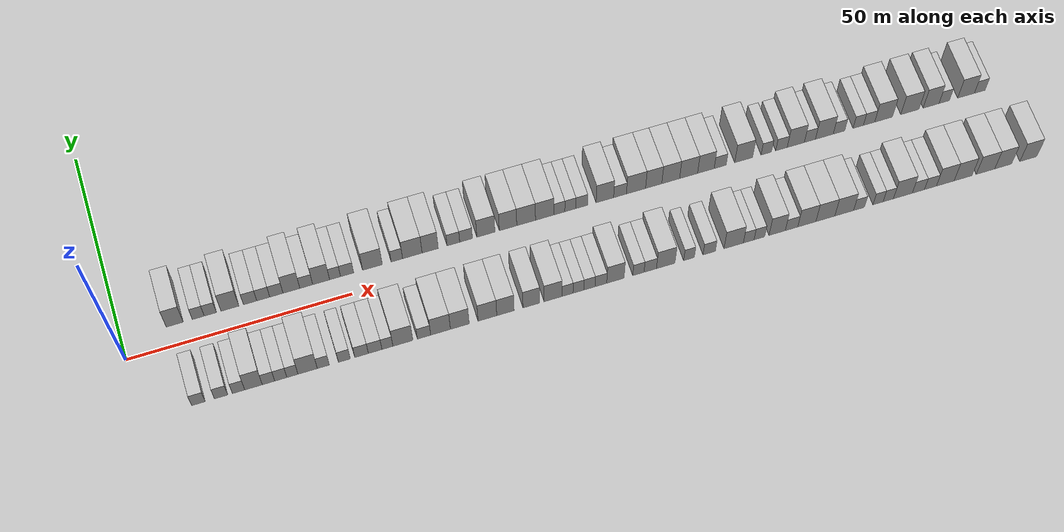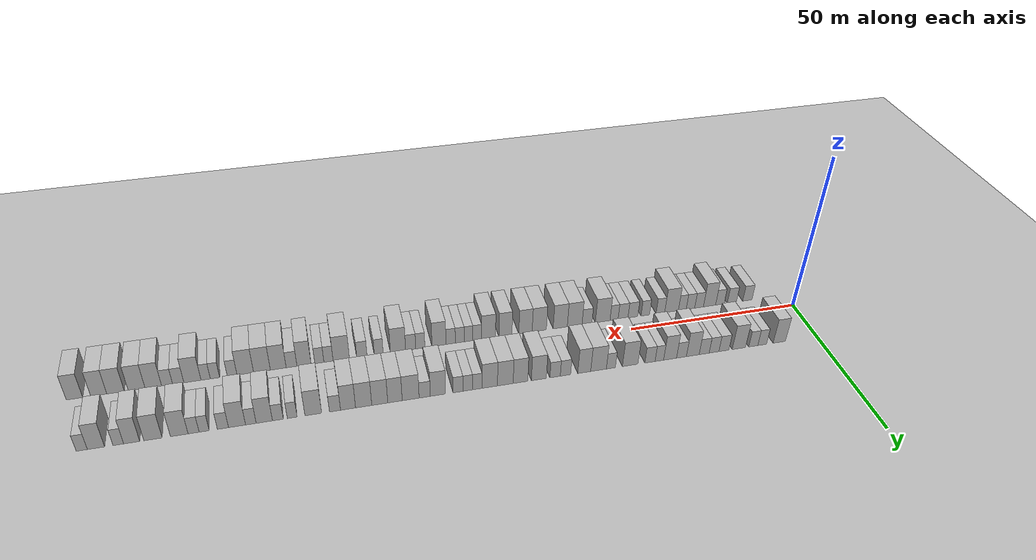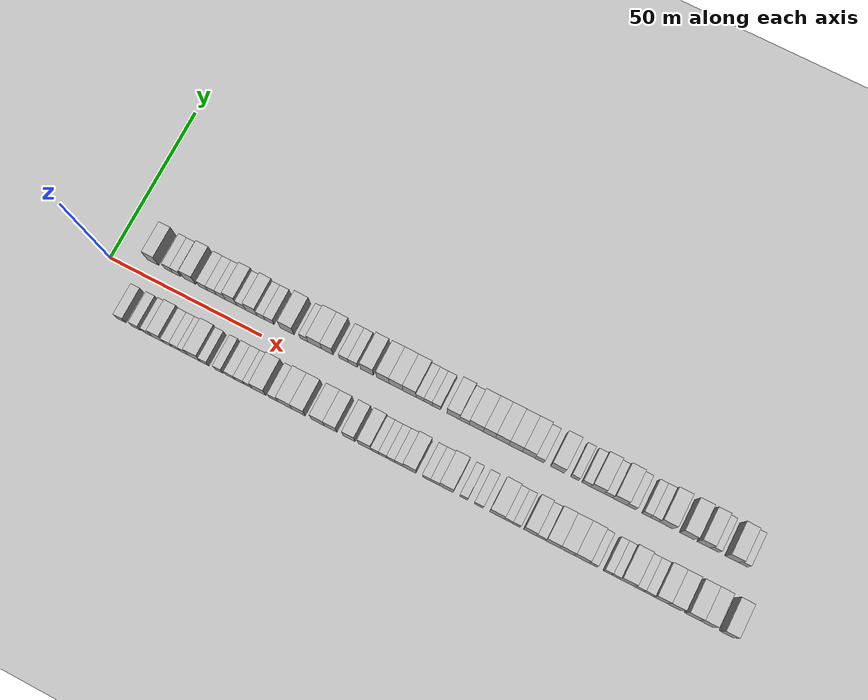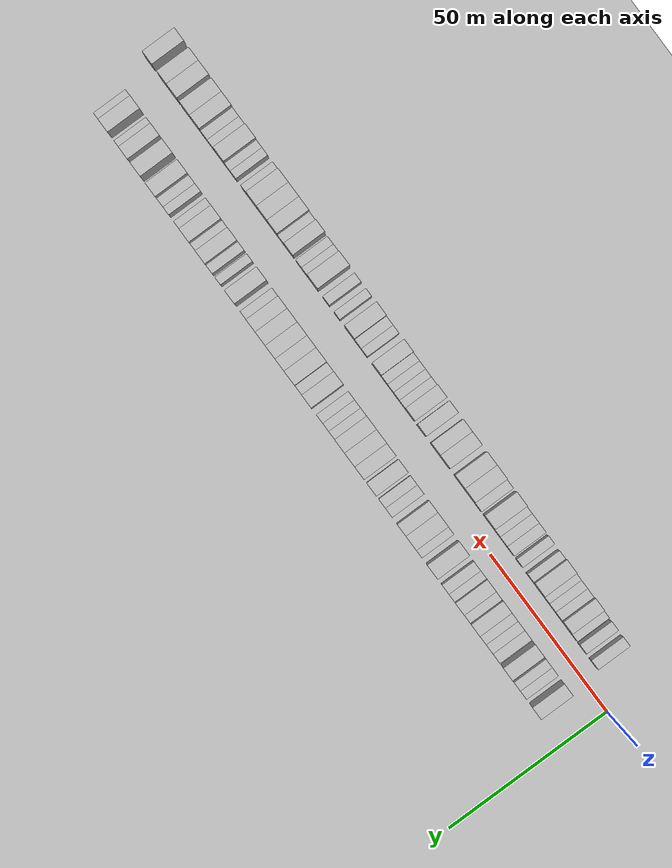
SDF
<?xml version="1.0" encoding="utf-8"?>

<sdf version="1.6">

   <world name="default">

      <gui fullscreen="0">

         <camera name="user_camera">

            <pose>-15 0 4.57585 0 0 0</pose>

            <view_controller>orbit</view_controller>

         </camera>

      </gui>

      <scene>

         <sky>

           <clouds>

             <speed>12</speed>

           </clouds>

         </sky>

         <ambient>0.4 0.4 0.4 1</ambient>

         <background>0.7 0.7 0.7 1</background>

         <shadows>1</shadows>

      </scene>

      <gravity>0 0 -9.8066</gravity>

      <magnetic_field>6e-06 2.3e-05 -4.2e-05</magnetic_field>

      <physics default="0" name="default_physics" type="ode">

         <ode>

            <solver>

               <type>quick</type>

               <iters>10</iters>

               <sor>1.0</sor>

               <use_dynamic_moi_rescaling>0</use_dynamic_moi_rescaling>

            </solver>

            <constraints>

               <cfm>0</cfm>

               <erp>0.2</erp>

               <contact_max_correcting_vel>100</contact_max_correcting_vel>

               <contact_surface_layer>0.001</contact_surface_layer>

            </constraints>

         </ode>

         <max_step_size>0.004</max_step_size>

         <real_time_factor>1</real_time_factor>

         <real_time_update_rate>250</real_time_update_rate>

      </physics>

      <light name="sun" type="directional">

         <cast_shadows>1</cast_shadows>

         <pose>0 0 10 0 0 0</pose>

         <diffuse>0.8 0.8 0.8 1</diffuse>

         <specular>0.2 0.2 0.2 1</specular>

         <attenuation>

            <range>1000</range>

            <constant>0.9</constant>

            <linear>0.01</linear>

            <quadratic>0.001</quadratic>

         </attenuation>

         <direction>-0.5 0.1 -0.9</direction>

      </light>

      <include>

         <name>ground_plane_1</name>

         <uri>model://HANNAS_ground_plane</uri>

         <pose>0 0 0  0 0 0</pose>

      </include>

      <include>

         <name>ground_plane_2</name>

         <uri>model://HANNAS_ground_plane</uri>

         <pose>100 0 0  0 0 0</pose>

      </include>

      <model name="building_1">

         <static>1</static>

         <pose frame="">11.8664 9.5000 0 0.000000 0.000000 1.570796</pose>

         <link name="link">

            <pose frame="">0 0 4.50 0 0 0</pose>

            <collision name="collision">

               <geometry>

                  <box>

                     <size>10.0000 3.7327 9.0000</size>

                  </box>

               </geometry>

               <max_contacts>10</max_contacts>

               <surface>

                  <contact>

                     <ode/>

                  </contact>

                  <bounce/>

                  <friction>

                     <torsional>

                        <ode/>

                     </torsional>

                     <ode/>

                  </friction>

               </surface>

            </collision>

            <visual name="visual">

               <cast_shadows>0</cast_shadows>

               <geometry>

                  <box>

                     <size>10.0000 3.7327 9.0000</size>

                  </box>

               </geometry>

               <material>

                  <script>

                     <uri>model://HANNAS_wall/materials/scripts</uri>

                     <uri>model://HANNAS_wall/materials/textures</uri>

                     <name>vrc/HANNAS_wall</name>

                  </script>

               </material>

            </visual>

            <self_collide>0</self_collide>

            <enable_wind>0</enable_wind>

            <kinematic>0</kinematic>

         </link>

      </model>

      <model name="building_2">

         <static>1</static>

         <pose frame="">17.0461 9.5000 0 0.000000 0.000000 1.570796</pose>

         <link name="link">

            <pose frame="">0 0 3.00 0 0 0</pose>

            <collision name="collision">

               <geometry>

                  <box>

                     <size>10.0000 2.6267 6.0000</size>

                  </box>

               </geometry>

               <max_contacts>10</max_contacts>

               <surface>

                  <contact>

                     <ode/>

                  </contact>

                  <bounce/>

                  <friction>

                     <torsional>

                        <ode/>

                     </torsional>

                     <ode/>

                  </friction>

               </surface>

            </collision>

            <visual name="visual">

               <cast_shadows>0</cast_shadows>

               <geometry>

                  <box>

                     <size>10.0000 2.6267 6.0000</size>

                  </box>

               </geometry>

               <material>

                  <script>

                     <uri>model://HANNAS_wall/materials/scripts</uri>

                     <uri>model://HANNAS_wall/materials/textures</uri>

                     <name>vrc/HANNAS_wall</name>

                  </script>

               </material>

            </visual>

            <self_collide>0</self_collide>

            <enable_wind>0</enable_wind>

            <kinematic>0</kinematic>

         </link>

      </model>

      <model name="building_3">

         <static>1</static>

         <pose frame="">19.7053 9.5000 0 0.000000 0.000000 1.570796</pose>

         <link name="link">

            <pose frame="">0 0 3.00 0 0 0</pose>

            <collision name="collision">

               <geometry>

                  <box>

                     <size>10.0000 2.6917 6.0000</size>

                  </box>

               </geometry>

               <max_contacts>10</max_contacts>

               <surface>

                  <contact>

                     <ode/>

                  </contact>

                  <bounce/>

                  <friction>

                     <torsional>

                        <ode/>

                     </torsional>

                     <ode/>

                  </friction>

               </surface>

            </collision>

            <visual name="visual">

               <cast_shadows>0</cast_shadows>

               <geometry>

                  <box>

                     <size>10.0000 2.6917 6.0000</size>

                  </box>

               </geometry>

               <material>

                  <script>

                     <uri>model://HANNAS_wall/materials/scripts</uri>

                     <uri>model://HANNAS_wall/materials/textures</uri>

                     <name>vrc/HANNAS_wall</name>

                  </script>

               </material>

            </visual>

            <self_collide>0</self_collide>

            <enable_wind>0</enable_wind>

            <kinematic>0</kinematic>

         </link>

      </model>

      <model name="building_4">

         <static>1</static>

         <pose frame="">24.0307 9.5000 0 0.000000 0.000000 1.570796</pose>

         <link name="link">

            <pose frame="">0 0 4.50 0 0 0</pose>

            <collision name="collision">

               <geometry>

                  <box>

                     <size>10.0000 3.9590 9.0000</size>

                  </box>

               </geometry>

               <max_contacts>10</max_contacts>

               <surface>

                  <contact>

                     <ode/>

                  </contact>

                  <bounce/>

                  <friction>

                     <torsional>

                        <ode/>

                     </torsional>

                     <ode/>

                  </friction>

               </surface>

            </collision>

            <visual name="visual">

               <cast_shadows>0</cast_shadows>

               <geometry>

                  <box>

                     <size>10.0000 3.9590 9.0000</size>

                  </box>

               </geometry>

               <material>

                  <script>

                     <uri>model://HANNAS_wall/materials/scripts</uri>

                     <uri>model://HANNAS_wall/materials/textures</uri>

                     <name>vrc/HANNAS_wall</name>

                  </script>

               </material>

            </visual>

            <self_collide>0</self_collide>

            <enable_wind>0</enable_wind>

            <kinematic>0</kinematic>

         </link>

      </model>

      <model name="building_5">

         <static>1</static>

         <pose frame="">28.4933 9.5000 0 0.000000 0.000000 1.570796</pose>

         <link name="link">

            <pose frame="">0 0 3.00 0 0 0</pose>

            <collision name="collision">

               <geometry>

                  <box>

                     <size>10.0000 2.9661 6.0000</size>

                  </box>

               </geometry>

               <max_contacts>10</max_contacts>

               <surface>

                  <contact>

                     <ode/>

                  </contact>

                  <bounce/>

                  <friction>

                     <torsional>

                        <ode/>

                     </torsional>

                     <ode/>

                  </friction>

               </surface>

            </collision>

            <visual name="visual">

               <cast_shadows>0</cast_shadows>

               <geometry>

                  <box>

                     <size>10.0000 2.9661 6.0000</size>

                  </box>

               </geometry>

               <material>

                  <script>

                     <uri>model://HANNAS_wall/materials/scripts</uri>

                     <uri>model://HANNAS_wall/materials/textures</uri>

                     <name>vrc/HANNAS_wall</name>

                  </script>

               </material>

            </visual>

            <self_collide>0</self_collide>

            <enable_wind>0</enable_wind>

            <kinematic>0</kinematic>

         </link>

      </model>

      <model name="building_6">

         <static>1</static>

         <pose frame="">31.4169 9.5000 0 0.000000 0.000000 1.570796</pose>

         <link name="link">

            <pose frame="">0 0 3.00 0 0 0</pose>

            <collision name="collision">

               <geometry>

                  <box>

                     <size>10.0000 2.8813 6.0000</size>

                  </box>

               </geometry>

               <max_contacts>10</max_contacts>

               <surface>

                  <contact>

                     <ode/>

                  </contact>

                  <bounce/>

                  <friction>

                     <torsional>

                        <ode/>

                     </torsional>

                     <ode/>

                  </friction>

               </surface>

            </collision>

            <visual name="visual">

               <cast_shadows>0</cast_shadows>

               <geometry>

                  <box>

                     <size>10.0000 2.8813 6.0000</size>

                  </box>

               </geometry>

               <material>

                  <script>

                     <uri>model://HANNAS_wall/materials/scripts</uri>

                     <uri>model://HANNAS_wall/materials/textures</uri>

                     <name>vrc/HANNAS_wall</name>

                  </script>

               </material>

            </visual>

            <self_collide>0</self_collide>

            <enable_wind>0</enable_wind>

            <kinematic>0</kinematic>

         </link>

      </model>

      <model name="building_7">

         <static>1</static>

         <pose frame="">34.3344 9.5000 0 0.000000 0.000000 1.570796</pose>

         <link name="link">

            <pose frame="">0 0 3.00 0 0 0</pose>

            <collision name="collision">

               <geometry>

                  <box>

                     <size>10.0000 2.9536 6.0000</size>

                  </box>

               </geometry>

               <max_contacts>10</max_contacts>

               <surface>

                  <contact>

                     <ode/>

                  </contact>

                  <bounce/>

                  <friction>

                     <torsional>

                        <ode/>

                     </torsional>

                     <ode/>

                  </friction>

               </surface>

            </collision>

            <visual name="visual">

               <cast_shadows>0</cast_shadows>

               <geometry>

                  <box>

                     <size>10.0000 2.9536 6.0000</size>

                  </box>

               </geometry>

               <material>

                  <script>

                     <uri>model://HANNAS_wall/materials/scripts</uri>

                     <uri>model://HANNAS_wall/materials/textures</uri>

                     <name>vrc/HANNAS_wall</name>

                  </script>

               </material>

            </visual>

            <self_collide>0</self_collide>

            <enable_wind>0</enable_wind>

            <kinematic>0</kinematic>

         </link>

      </model>

      <model name="building_8">

         <static>1</static>

         <pose frame="">37.6866 9.5000 0 0.000000 0.000000 1.570796</pose>

         <link name="link">

            <pose frame="">0 0 4.50 0 0 0</pose>

            <collision name="collision">

               <geometry>

                  <box>

                     <size>10.0000 3.7509 9.0000</size>

                  </box>

               </geometry>

               <max_contacts>10</max_contacts>

               <surface>

                  <contact>

                     <ode/>

                  </contact>

                  <bounce/>

                  <friction>

                     <torsional>

                        <ode/>

                     </torsional>

                     <ode/>

                  </friction>

               </surface>

            </collision>

            <visual name="visual">

               <cast_shadows>0</cast_shadows>

               <geometry>

                  <box>

                     <size>10.0000 3.7509 9.0000</size>

                  </box>

               </geometry>

               <material>

                  <script>

                     <uri>model://HANNAS_wall/materials/scripts</uri>

                     <uri>model://HANNAS_wall/materials/textures</uri>

                     <name>vrc/HANNAS_wall</name>

                  </script>

               </material>

            </visual>

            <self_collide>0</self_collide>

            <enable_wind>0</enable_wind>

            <kinematic>0</kinematic>

         </link>

      </model>

      <model name="building_9">

         <static>1</static>

         <pose frame="">40.9992 9.5000 0 0.000000 0.000000 1.570796</pose>

         <link name="link">

            <pose frame="">0 0 3.00 0 0 0</pose>

            <collision name="collision">

               <geometry>

                  <box>

                     <size>10.0000 2.8742 6.0000</size>

                  </box>

               </geometry>

               <max_contacts>10</max_contacts>

               <surface>

                  <contact>

                     <ode/>

                  </contact>

                  <bounce/>

                  <friction>

                     <torsional>

                        <ode/>

                     </torsional>

                     <ode/>

                  </friction>

               </surface>

            </collision>

            <visual name="visual">

               <cast_shadows>0</cast_shadows>

               <geometry>

                  <box>

                     <size>10.0000 2.8742 6.0000</size>

                  </box>

               </geometry>

               <material>

                  <script>

                     <uri>model://HANNAS_wall/materials/scripts</uri>

                     <uri>model://HANNAS_wall/materials/textures</uri>

                     <name>vrc/HANNAS_wall</name>

                  </script>

               </material>

            </visual>

            <self_collide>0</self_collide>

            <enable_wind>0</enable_wind>

            <kinematic>0</kinematic>

         </link>

      </model>

      <model name="building_10">

         <static>1</static>

         <pose frame="">44.3162 9.5000 0 0.000000 0.000000 1.570796</pose>

         <link name="link">

            <pose frame="">0 0 4.50 0 0 0</pose>

            <collision name="collision">

               <geometry>

                  <box>

                     <size>10.0000 3.7599 9.0000</size>

                  </box>

               </geometry>

               <max_contacts>10</max_contacts>

               <surface>

                  <contact>

                     <ode/>

                  </contact>

                  <bounce/>

                  <friction>

                     <torsional>

                        <ode/>

                     </torsional>

                     <ode/>

                  </friction>

               </surface>

            </collision>

            <visual name="visual">

               <cast_shadows>0</cast_shadows>

               <geometry>

                  <box>

                     <size>10.0000 3.7599 9.0000</size>

                  </box>

               </geometry>

               <material>

                  <script>

                     <uri>model://HANNAS_wall/materials/scripts</uri>

                     <uri>model://HANNAS_wall/materials/textures</uri>

                     <name>vrc/HANNAS_wall</name>

                  </script>

               </material>

            </visual>

            <self_collide>0</self_collide>

            <enable_wind>0</enable_wind>

            <kinematic>0</kinematic>

         </link>

      </model>

      <model name="building_11">

         <static>1</static>

         <pose frame="">47.4281 9.5000 0 0.000000 0.000000 1.570796</pose>

         <link name="link">

            <pose frame="">0 0 3.00 0 0 0</pose>

            <collision name="collision">

               <geometry>

                  <box>

                     <size>10.0000 2.4638 6.0000</size>

                  </box>

               </geometry>

               <max_contacts>10</max_contacts>

               <surface>

                  <contact>

                     <ode/>

                  </contact>

                  <bounce/>

                  <friction>

                     <torsional>

                        <ode/>

                     </torsional>

                     <ode/>

                  </friction>

               </surface>

            </collision>

            <visual name="visual">

               <cast_shadows>0</cast_shadows>

               <geometry>

                  <box>

                     <size>10.0000 2.4638 6.0000</size>

                  </box>

               </geometry>

               <material>

                  <script>

                     <uri>model://HANNAS_wall/materials/scripts</uri>

                     <uri>model://HANNAS_wall/materials/textures</uri>

                     <name>vrc/HANNAS_wall</name>

                  </script>

               </material>

            </visual>

            <self_collide>0</self_collide>

            <enable_wind>0</enable_wind>

            <kinematic>0</kinematic>

         </link>

      </model>

      <model name="building_12">

         <static>1</static>

         <pose frame="">50.1368 9.5000 0 0.000000 0.000000 1.570796</pose>

         <link name="link">

            <pose frame="">0 0 3.00 0 0 0</pose>

            <collision name="collision">

               <geometry>

                  <box>

                     <size>10.0000 2.9536 6.0000</size>

                  </box>

               </geometry>

               <max_contacts>10</max_contacts>

               <surface>

                  <contact>

                     <ode/>

                  </contact>

                  <bounce/>

                  <friction>

                     <torsional>

                        <ode/>

                     </torsional>

                     <ode/>

                  </friction>

               </surface>

            </collision>

            <visual name="visual">

               <cast_shadows>0</cast_shadows>

               <geometry>

                  <box>

                     <size>10.0000 2.9536 6.0000</size>

                  </box>

               </geometry>

               <material>

                  <script>

                     <uri>model://HANNAS_wall/materials/scripts</uri>

                     <uri>model://HANNAS_wall/materials/textures</uri>

                     <name>vrc/HANNAS_wall</name>

                  </script>

               </material>

            </visual>

            <self_collide>0</self_collide>

            <enable_wind>0</enable_wind>

            <kinematic>0</kinematic>

         </link>

      </model>

      <model name="building_13">

         <static>1</static>

         <pose frame="">55.8347 9.5000 0 0.000000 0.000000 1.570796</pose>

         <link name="link">

            <pose frame="">0 0 4.50 0 0 0</pose>

            <collision name="collision">

               <geometry>

                  <box>

                     <size>10.0000 4.4424 9.0000</size>

                  </box>

               </geometry>

               <max_contacts>10</max_contacts>

               <surface>

                  <contact>

                     <ode/>

                  </contact>

                  <bounce/>

                  <friction>

                     <torsional>

                        <ode/>

                     </torsional>

                     <ode/>

                  </friction>

               </surface>

            </collision>

            <visual name="visual">

               <cast_shadows>0</cast_shadows>

               <geometry>

                  <box>

                     <size>10.0000 4.4424 9.0000</size>

                  </box>

               </geometry>

               <material>

                  <script>

                     <uri>model://HANNAS_wall/materials/scripts</uri>

                     <uri>model://HANNAS_wall/materials/textures</uri>

                     <name>vrc/HANNAS_wall</name>

                  </script>

               </material>

            </visual>

            <self_collide>0</self_collide>

            <enable_wind>0</enable_wind>

            <kinematic>0</kinematic>

         </link>

      </model>

      <model name="building_14">

         <static>1</static>

         <pose frame="">61.3404 9.5000 0 0.000000 0.000000 1.570796</pose>

         <link name="link">

            <pose frame="">0 0 3.00 0 0 0</pose>

            <collision name="collision">

               <geometry>

                  <box>

                     <size>10.0000 2.5689 6.0000</size>

                  </box>

               </geometry>

               <max_contacts>10</max_contacts>

               <surface>

                  <contact>

                     <ode/>

                  </contact>

                  <bounce/>

                  <friction>

                     <torsional>

                        <ode/>

                     </torsional>

                     <ode/>

                  </friction>

               </surface>

            </collision>

            <visual name="visual">

               <cast_shadows>0</cast_shadows>

               <geometry>

                  <box>

                     <size>10.0000 2.5689 6.0000</size>

                  </box>

               </geometry>

               <material>

                  <script>

                     <uri>model://HANNAS_wall/materials/scripts</uri>

                     <uri>model://HANNAS_wall/materials/textures</uri>

                     <name>vrc/HANNAS_wall</name>

                  </script>

               </material>

            </visual>

            <self_collide>0</self_collide>

            <enable_wind>0</enable_wind>

            <kinematic>0</kinematic>

         </link>

      </model>

      <model name="building_15">

         <static>1</static>

         <pose frame="">64.8377 9.5000 0 0.000000 0.000000 1.570796</pose>

         <link name="link">

            <pose frame="">0 0 4.50 0 0 0</pose>

            <collision name="collision">

               <geometry>

                  <box>

                     <size>10.0000 4.4256 9.0000</size>

                  </box>

               </geometry>

               <max_contacts>10</max_contacts>

               <surface>

                  <contact>

                     <ode/>

                  </contact>

                  <bounce/>

                  <friction>

                     <torsional>

                        <ode/>

                     </torsional>

                     <ode/>

                  </friction>

               </surface>

            </collision>

            <visual name="visual">

               <cast_shadows>0</cast_shadows>

               <geometry>

                  <box>

                     <size>10.0000 4.4256 9.0000</size>

                  </box>

               </geometry>

               <material>

                  <script>

                     <uri>model://HANNAS_wall/materials/scripts</uri>

                     <uri>model://HANNAS_wall/materials/textures</uri>

                     <name>vrc/HANNAS_wall</name>

                  </script>

               </material>

            </visual>

            <self_collide>0</self_collide>

            <enable_wind>0</enable_wind>

            <kinematic>0</kinematic>

         </link>

      </model>

      <model name="building_16">

         <static>1</static>

         <pose frame="">68.8795 9.5000 0 0.000000 0.000000 1.570796</pose>

         <link name="link">

            <pose frame="">0 0 4.50 0 0 0</pose>

            <collision name="collision">

               <geometry>

                  <box>

                     <size>10.0000 3.6580 9.0000</size>

                  </box>

               </geometry>

               <max_contacts>10</max_contacts>

               <surface>

                  <contact>

                     <ode/>

                  </contact>

                  <bounce/>

                  <friction>

                     <torsional>

                        <ode/>

                     </torsional>

                     <ode/>

                  </friction>

               </surface>

            </collision>

            <visual name="visual">

               <cast_shadows>0</cast_shadows>

               <geometry>

                  <box>

                     <size>10.0000 3.6580 9.0000</size>

                  </box>

               </geometry>

               <material>

                  <script>

                     <uri>model://HANNAS_wall/materials/scripts</uri>

                     <uri>model://HANNAS_wall/materials/textures</uri>

                     <name>vrc/HANNAS_wall</name>

                  </script>

               </material>

            </visual>

            <self_collide>0</self_collide>

            <enable_wind>0</enable_wind>

            <kinematic>0</kinematic>

         </link>

      </model>

      <model name="building_17">

         <static>1</static>

         <pose frame="">74.1507 9.5000 0 0.000000 0.000000 1.570796</pose>

         <link name="link">

            <pose frame="">0 0 3.00 0 0 0</pose>

            <collision name="collision">

               <geometry>

                  <box>

                     <size>10.0000 2.8844 6.0000</size>

                  </box>

               </geometry>

               <max_contacts>10</max_contacts>

               <surface>

                  <contact>

                     <ode/>

                  </contact>

                  <bounce/>

                  <friction>

                     <torsional>

                        <ode/>

                     </torsional>

                     <ode/>

                  </friction>

               </surface>

            </collision>

            <visual name="visual">

               <cast_shadows>0</cast_shadows>

               <geometry>

                  <box>

                     <size>10.0000 2.8844 6.0000</size>

                  </box>

               </geometry>

               <material>

                  <script>

                     <uri>model://HANNAS_wall/materials/scripts</uri>

                     <uri>model://HANNAS_wall/materials/textures</uri>

                     <name>vrc/HANNAS_wall</name>

                  </script>

               </material>

            </visual>

            <self_collide>0</self_collide>

            <enable_wind>0</enable_wind>

            <kinematic>0</kinematic>

         </link>

      </model>

      <model name="building_18">

         <static>1</static>

         <pose frame="">77.0405 9.5000 0 0.000000 0.000000 1.570796</pose>

         <link name="link">

            <pose frame="">0 0 3.00 0 0 0</pose>

            <collision name="collision">

               <geometry>

                  <box>

                     <size>10.0000 2.8953 6.0000</size>

                  </box>

               </geometry>

               <max_contacts>10</max_contacts>

               <surface>

                  <contact>

                     <ode/>

                  </contact>

                  <bounce/>

                  <friction>

                     <torsional>

                        <ode/>

                     </torsional>

                     <ode/>

                  </friction>

               </surface>

            </collision>

            <visual name="visual">

               <cast_shadows>0</cast_shadows>

               <geometry>

                  <box>

                     <size>10.0000 2.8953 6.0000</size>

                  </box>

               </geometry>

               <material>

                  <script>

                     <uri>model://HANNAS_wall/materials/scripts</uri>

                     <uri>model://HANNAS_wall/materials/textures</uri>

                     <name>vrc/HANNAS_wall</name>

                  </script>

               </material>

            </visual>

            <self_collide>0</self_collide>

            <enable_wind>0</enable_wind>

            <kinematic>0</kinematic>

         </link>

      </model>

      <model name="building_19">

         <static>1</static>

         <pose frame="">81.5546 9.5000 0 0.000000 0.000000 1.570796</pose>

         <link name="link">

            <pose frame="">0 0 4.50 0 0 0</pose>

            <collision name="collision">

               <geometry>

                  <box>

                     <size>10.0000 4.1329 9.0000</size>

                  </box>

               </geometry>

               <max_contacts>10</max_contacts>

               <surface>

                  <contact>

                     <ode/>

                  </contact>

                  <bounce/>

                  <friction>

                     <torsional>

                        <ode/>

                     </torsional>

                     <ode/>

                  </friction>

               </surface>

            </collision>

            <visual name="visual">

               <cast_shadows>0</cast_shadows>

               <geometry>

                  <box>

                     <size>10.0000 4.1329 9.0000</size>

                  </box>

               </geometry>

               <material>

                  <script>

                     <uri>model://HANNAS_wall/materials/scripts</uri>

                     <uri>model://HANNAS_wall/materials/textures</uri>

                     <name>vrc/HANNAS_wall</name>

                  </script>

               </material>

            </visual>

            <self_collide>0</self_collide>

            <enable_wind>0</enable_wind>

            <kinematic>0</kinematic>

         </link>

      </model>

      <model name="building_20">

         <static>1</static>

         <pose frame="">86.6228 9.5000 0 0.000000 0.000000 1.570796</pose>

         <link name="link">

            <pose frame="">0 0 4.50 0 0 0</pose>

            <collision name="collision">

               <geometry>

                  <box>

                     <size>10.0000 4.0037 9.0000</size>

                  </box>

               </geometry>

               <max_contacts>10</max_contacts>

               <surface>

                  <contact>

                     <ode/>

                  </contact>

                  <bounce/>

                  <friction>

                     <torsional>

                        <ode/>

                     </torsional>

                     <ode/>

                  </friction>

               </surface>

            </collision>

            <visual name="visual">

               <cast_shadows>0</cast_shadows>

               <geometry>

                  <box>

                     <size>10.0000 4.0037 9.0000</size>

                  </box>

               </geometry>

               <material>

                  <script>

                     <uri>model://HANNAS_wall/materials/scripts</uri>

                     <uri>model://HANNAS_wall/materials/textures</uri>

                     <name>vrc/HANNAS_wall</name>

                  </script>

               </material>

            </visual>

            <self_collide>0</self_collide>

            <enable_wind>0</enable_wind>

            <kinematic>0</kinematic>

         </link>

      </model>

      <model name="building_21">

         <static>1</static>

         <pose frame="">90.7758 9.5000 0 0.000000 0.000000 1.570796</pose>

         <link name="link">

            <pose frame="">0 0 4.50 0 0 0</pose>

            <collision name="collision">

               <geometry>

                  <box>

                     <size>10.0000 4.3022 9.0000</size>

                  </box>

               </geometry>

               <max_contacts>10</max_contacts>

               <surface>

                  <contact>

                     <ode/>

                  </contact>

                  <bounce/>

                  <friction>

                     <torsional>

                        <ode/>

                     </torsional>

                     <ode/>

                  </friction>

               </surface>

            </collision>

            <visual name="visual">

               <cast_shadows>0</cast_shadows>

               <geometry>

                  <box>

                     <size>10.0000 4.3022 9.0000</size>

                  </box>

               </geometry>

               <material>

                  <script>

                     <uri>model://HANNAS_wall/materials/scripts</uri>

                     <uri>model://HANNAS_wall/materials/textures</uri>

                     <name>vrc/HANNAS_wall</name>

                  </script>

               </material>

            </visual>

            <self_collide>0</self_collide>

            <enable_wind>0</enable_wind>

            <kinematic>0</kinematic>

         </link>

      </model>

      <model name="building_22">

         <static>1</static>

         <pose frame="">95.0272 9.5000 0 0.000000 0.000000 1.570796</pose>

         <link name="link">

            <pose frame="">0 0 4.50 0 0 0</pose>

            <collision name="collision">

               <geometry>

                  <box>

                     <size>10.0000 4.2006 9.0000</size>

                  </box>

               </geometry>

               <max_contacts>10</max_contacts>

               <surface>

                  <contact>

                     <ode/>

                  </contact>

                  <bounce/>

                  <friction>

                     <torsional>

                        <ode/>

                     </torsional>

                     <ode/>

                  </friction>

               </surface>

            </collision>

            <visual name="visual">

               <cast_shadows>0</cast_shadows>

               <geometry>

                  <box>

                     <size>10.0000 4.2006 9.0000</size>

                  </box>

               </geometry>

               <material>

                  <script>

                     <uri>model://HANNAS_wall/materials/scripts</uri>

                     <uri>model://HANNAS_wall/materials/textures</uri>

                     <name>vrc/HANNAS_wall</name>

                  </script>

               </material>

            </visual>

            <self_collide>0</self_collide>

            <enable_wind>0</enable_wind>

            <kinematic>0</kinematic>

         </link>

      </model>

      <model name="building_23">

         <static>1</static>

         <pose frame="">98.4095 9.5000 0 0.000000 0.000000 1.570796</pose>

         <link name="link">

            <pose frame="">0 0 3.00 0 0 0</pose>

            <collision name="collision">

               <geometry>

                  <box>

                     <size>10.0000 2.5641 6.0000</size>

                  </box>

               </geometry>

               <max_contacts>10</max_contacts>

               <surface>

                  <contact>

                     <ode/>

                  </contact>

                  <bounce/>

                  <friction>

                     <torsional>

                        <ode/>

                     </torsional>

                     <ode/>

                  </friction>

               </surface>

            </collision>

            <visual name="visual">

               <cast_shadows>0</cast_shadows>

               <geometry>

                  <box>

                     <size>10.0000 2.5641 6.0000</size>

                  </box>

               </geometry>

               <material>

                  <script>

                     <uri>model://HANNAS_wall/materials/scripts</uri>

                     <uri>model://HANNAS_wall/materials/textures</uri>

                     <name>vrc/HANNAS_wall</name>

                  </script>

               </material>

            </visual>

            <self_collide>0</self_collide>

            <enable_wind>0</enable_wind>

            <kinematic>0</kinematic>

         </link>

      </model>

      <model name="building_24">

         <static>1</static>

         <pose frame="">100.9636 9.5000 0 0.000000 0.000000 1.570796</pose>

         <link name="link">

            <pose frame="">0 0 3.00 0 0 0</pose>

            <collision name="collision">

               <geometry>

                  <box>

                     <size>10.0000 2.5440 6.0000</size>

                  </box>

               </geometry>

               <max_contacts>10</max_contacts>

               <surface>

                  <contact>

                     <ode/>

                  </contact>

                  <bounce/>

                  <friction>

                     <torsional>

                        <ode/>

                     </torsional>

                     <ode/>

                  </friction>

               </surface>

            </collision>

            <visual name="visual">

               <cast_shadows>0</cast_shadows>

               <geometry>

                  <box>

                     <size>10.0000 2.5440 6.0000</size>

                  </box>

               </geometry>

               <material>

                  <script>

                     <uri>model://HANNAS_wall/materials/scripts</uri>

                     <uri>model://HANNAS_wall/materials/textures</uri>

                     <name>vrc/HANNAS_wall</name>

                  </script>

               </material>

            </visual>

            <self_collide>0</self_collide>

            <enable_wind>0</enable_wind>

            <kinematic>0</kinematic>

         </link>

      </model>

      <model name="building_25">

         <static>1</static>

         <pose frame="">103.5814 9.5000 0 0.000000 0.000000 1.570796</pose>

         <link name="link">

            <pose frame="">0 0 3.00 0 0 0</pose>

            <collision name="collision">

               <geometry>

                  <box>

                     <size>10.0000 2.6917 6.0000</size>

                  </box>

               </geometry>

               <max_contacts>10</max_contacts>

               <surface>

                  <contact>

                     <ode/>

                  </contact>

                  <bounce/>

                  <friction>

                     <torsional>

                        <ode/>

                     </torsional>

                     <ode/>

                  </friction>

               </surface>

            </collision>

            <visual name="visual">

               <cast_shadows>0</cast_shadows>

               <geometry>

                  <box>

                     <size>10.0000 2.6917 6.0000</size>

                  </box>

               </geometry>

               <material>

                  <script>

                     <uri>model://HANNAS_wall/materials/scripts</uri>

                     <uri>model://HANNAS_wall/materials/textures</uri>

                     <name>vrc/HANNAS_wall</name>

                  </script>

               </material>

            </visual>

            <self_collide>0</self_collide>

            <enable_wind>0</enable_wind>

            <kinematic>0</kinematic>

         </link>

      </model>

      <model name="building_26">

         <static>1</static>

         <pose frame="">108.9583 9.5000 0 0.000000 0.000000 1.570796</pose>

         <link name="link">

            <pose frame="">0 0 4.50 0 0 0</pose>

            <collision name="collision">

               <geometry>

                  <box>

                     <size>10.0000 4.0622 9.0000</size>

                  </box>

               </geometry>

               <max_contacts>10</max_contacts>

               <surface>

                  <contact>

                     <ode/>

                  </contact>

                  <bounce/>

                  <friction>

                     <torsional>

                        <ode/>

                     </torsional>

                     <ode/>

                  </friction>

               </surface>

            </collision>

            <visual name="visual">

               <cast_shadows>0</cast_shadows>

               <geometry>

                  <box>

                     <size>10.0000 4.0622 9.0000</size>

                  </box>

               </geometry>

               <material>

                  <script>

                     <uri>model://HANNAS_wall/materials/scripts</uri>

                     <uri>model://HANNAS_wall/materials/textures</uri>

                     <name>vrc/HANNAS_wall</name>

                  </script>

               </material>

            </visual>

            <self_collide>0</self_collide>

            <enable_wind>0</enable_wind>

            <kinematic>0</kinematic>

         </link>

      </model>

      <model name="building_27">

         <static>1</static>

         <pose frame="">112.4739 9.5000 0 0.000000 0.000000 1.570796</pose>

         <link name="link">

            <pose frame="">0 0 3.00 0 0 0</pose>

            <collision name="collision">

               <geometry>

                  <box>

                     <size>10.0000 2.9690 6.0000</size>

                  </box>

               </geometry>

               <max_contacts>10</max_contacts>

               <surface>

                  <contact>

                     <ode/>

                  </contact>

                  <bounce/>

                  <friction>

                     <torsional>

                        <ode/>

                     </torsional>

                     <ode/>

                  </friction>

               </surface>

            </collision>

            <visual name="visual">

               <cast_shadows>0</cast_shadows>

               <geometry>

                  <box>

                     <size>10.0000 2.9690 6.0000</size>

                  </box>

               </geometry>

               <material>

                  <script>

                     <uri>model://HANNAS_wall/materials/scripts</uri>

                     <uri>model://HANNAS_wall/materials/textures</uri>

                     <name>vrc/HANNAS_wall</name>

                  </script>

               </material>

            </visual>

            <self_collide>0</self_collide>

            <enable_wind>0</enable_wind>

            <kinematic>0</kinematic>

         </link>

      </model>

      <model name="building_28">

         <static>1</static>

         <pose frame="">116.1923 9.5000 0 0.000000 0.000000 1.570796</pose>

         <link name="link">

            <pose frame="">0 0 4.50 0 0 0</pose>

            <collision name="collision">

               <geometry>

                  <box>

                     <size>10.0000 4.4678 9.0000</size>

                  </box>

               </geometry>

               <max_contacts>10</max_contacts>

               <surface>

                  <contact>

                     <ode/>

                  </contact>

                  <bounce/>

                  <friction>

                     <torsional>

                        <ode/>

                     </torsional>

                     <ode/>

                  </friction>

               </surface>

            </collision>

            <visual name="visual">

               <cast_shadows>0</cast_shadows>

               <geometry>

                  <box>

                     <size>10.0000 4.4678 9.0000</size>

                  </box>

               </geometry>

               <material>

                  <script>

                     <uri>model://HANNAS_wall/materials/scripts</uri>

                     <uri>model://HANNAS_wall/materials/textures</uri>

                     <name>vrc/HANNAS_wall</name>

                  </script>

               </material>

            </visual>

            <self_collide>0</self_collide>

            <enable_wind>0</enable_wind>

            <kinematic>0</kinematic>

         </link>

      </model>

      <model name="building_29">

         <static>1</static>

         <pose frame="">120.3228 9.5000 0 0.000000 0.000000 1.570796</pose>

         <link name="link">

            <pose frame="">0 0 4.50 0 0 0</pose>

            <collision name="collision">

               <geometry>

                  <box>

                     <size>10.0000 3.7932 9.0000</size>

                  </box>

               </geometry>

               <max_contacts>10</max_contacts>

               <surface>

                  <contact>

                     <ode/>

                  </contact>

                  <bounce/>

                  <friction>

                     <torsional>

                        <ode/>

                     </torsional>

                     <ode/>

                  </friction>

               </surface>

            </collision>

            <visual name="visual">

               <cast_shadows>0</cast_shadows>

               <geometry>

                  <box>

                     <size>10.0000 3.7932 9.0000</size>

                  </box>

               </geometry>

               <material>

                  <script>

                     <uri>model://HANNAS_wall/materials/scripts</uri>

                     <uri>model://HANNAS_wall/materials/textures</uri>

                     <name>vrc/HANNAS_wall</name>

                  </script>

               </material>

            </visual>

            <self_collide>0</self_collide>

            <enable_wind>0</enable_wind>

            <kinematic>0</kinematic>

         </link>

      </model>

      <model name="building_30">

         <static>1</static>

         <pose frame="">124.3046 9.5000 0 0.000000 0.000000 1.570796</pose>

         <link name="link">

            <pose frame="">0 0 4.50 0 0 0</pose>

            <collision name="collision">

               <geometry>

                  <box>

                     <size>10.0000 4.1702 9.0000</size>

                  </box>

               </geometry>

               <max_contacts>10</max_contacts>

               <surface>

                  <contact>

                     <ode/>

                  </contact>

                  <bounce/>

                  <friction>

                     <torsional>

                        <ode/>

                     </torsional>

                     <ode/>

                  </friction>

               </surface>

            </collision>

            <visual name="visual">

               <cast_shadows>0</cast_shadows>

               <geometry>

                  <box>

                     <size>10.0000 4.1702 9.0000</size>

                  </box>

               </geometry>

               <material>

                  <script>

                     <uri>model://HANNAS_wall/materials/scripts</uri>

                     <uri>model://HANNAS_wall/materials/textures</uri>

                     <name>vrc/HANNAS_wall</name>

                  </script>

               </material>

            </visual>

            <self_collide>0</self_collide>

            <enable_wind>0</enable_wind>

            <kinematic>0</kinematic>

         </link>

      </model>

      <model name="building_31">

         <static>1</static>

         <pose frame="">128.4947 9.5000 0 0.000000 0.000000 1.570796</pose>

         <link name="link">

            <pose frame="">0 0 4.50 0 0 0</pose>

            <collision name="collision">

               <geometry>

                  <box>

                     <size>10.0000 4.2100 9.0000</size>

                  </box>

               </geometry>

               <max_contacts>10</max_contacts>

               <surface>

                  <contact>

                     <ode/>

                  </contact>

                  <bounce/>

                  <friction>

                     <torsional>

                        <ode/>

                     </torsional>

                     <ode/>

                  </friction>

               </surface>

            </collision>

            <visual name="visual">

               <cast_shadows>0</cast_shadows>

               <geometry>

                  <box>

                     <size>10.0000 4.2100 9.0000</size>

                  </box>

               </geometry>

               <material>

                  <script>

                     <uri>model://HANNAS_wall/materials/scripts</uri>

                     <uri>model://HANNAS_wall/materials/textures</uri>

                     <name>vrc/HANNAS_wall</name>

                  </script>

               </material>

            </visual>

            <self_collide>0</self_collide>

            <enable_wind>0</enable_wind>

            <kinematic>0</kinematic>

         </link>

      </model>

      <model name="building_32">

         <static>1</static>

         <pose frame="">132.5430 9.5000 0 0.000000 0.000000 1.570796</pose>

         <link name="link">

            <pose frame="">0 0 4.50 0 0 0</pose>

            <collision name="collision">

               <geometry>

                  <box>

                     <size>10.0000 3.8865 9.0000</size>

                  </box>

               </geometry>

               <max_contacts>10</max_contacts>

               <surface>

                  <contact>

                     <ode/>

                  </contact>

                  <bounce/>

                  <friction>

                     <torsional>

                        <ode/>

                     </torsional>

                     <ode/>

                  </friction>

               </surface>

            </collision>

            <visual name="visual">

               <cast_shadows>0</cast_shadows>

               <geometry>

                  <box>

                     <size>10.0000 3.8865 9.0000</size>

                  </box>

               </geometry>

               <material>

                  <script>

                     <uri>model://HANNAS_wall/materials/scripts</uri>

                     <uri>model://HANNAS_wall/materials/textures</uri>

                     <name>vrc/HANNAS_wall</name>

                  </script>

               </material>

            </visual>

            <self_collide>0</self_collide>

            <enable_wind>0</enable_wind>

            <kinematic>0</kinematic>

         </link>

      </model>

      <model name="building_33">

         <static>1</static>

         <pose frame="">135.9067 9.5000 0 0.000000 0.000000 1.570796</pose>

         <link name="link">

            <pose frame="">0 0 3.00 0 0 0</pose>

            <collision name="collision">

               <geometry>

                  <box>

                     <size>10.0000 2.8411 6.0000</size>

                  </box>

               </geometry>

               <max_contacts>10</max_contacts>

               <surface>

                  <contact>

                     <ode/>

                  </contact>

                  <bounce/>

                  <friction>

                     <torsional>

                        <ode/>

                     </torsional>

                     <ode/>

                  </friction>

               </surface>

            </collision>

            <visual name="visual">

               <cast_shadows>0</cast_shadows>

               <geometry>

                  <box>

                     <size>10.0000 2.8411 6.0000</size>

                  </box>

               </geometry>

               <material>

                  <script>

                     <uri>model://HANNAS_wall/materials/scripts</uri>

                     <uri>model://HANNAS_wall/materials/textures</uri>

                     <name>vrc/HANNAS_wall</name>

                  </script>

               </material>

            </visual>

            <self_collide>0</self_collide>

            <enable_wind>0</enable_wind>

            <kinematic>0</kinematic>

         </link>

      </model>

      <model name="building_34">

         <static>1</static>

         <pose frame="">141.4555 9.5000 0 0.000000 0.000000 1.570796</pose>

         <link name="link">

            <pose frame="">0 0 4.50 0 0 0</pose>

            <collision name="collision">

               <geometry>

                  <box>

                     <size>10.0000 4.2565 9.0000</size>

                  </box>

               </geometry>

               <max_contacts>10</max_contacts>

               <surface>

                  <contact>

                     <ode/>

                  </contact>

                  <bounce/>

                  <friction>

                     <torsional>

                        <ode/>

                     </torsional>

                     <ode/>

                  </friction>

               </surface>

            </collision>

            <visual name="visual">

               <cast_shadows>0</cast_shadows>

               <geometry>

                  <box>

                     <size>10.0000 4.2565 9.0000</size>

                  </box>

               </geometry>

               <material>

                  <script>

                     <uri>model://HANNAS_wall/materials/scripts</uri>

                     <uri>model://HANNAS_wall/materials/textures</uri>

                     <name>vrc/HANNAS_wall</name>

                  </script>

               </material>

            </visual>

            <self_collide>0</self_collide>

            <enable_wind>0</enable_wind>

            <kinematic>0</kinematic>

         </link>

      </model>

      <model name="building_35">

         <static>1</static>

         <pose frame="">146.8189 9.5000 0 0.000000 0.000000 1.570796</pose>

         <link name="link">

            <pose frame="">0 0 3.00 0 0 0</pose>

            <collision name="collision">

               <geometry>

                  <box>

                     <size>10.0000 2.4702 6.0000</size>

                  </box>

               </geometry>

               <max_contacts>10</max_contacts>

               <surface>

                  <contact>

                     <ode/>

                  </contact>

                  <bounce/>

                  <friction>

                     <torsional>

                        <ode/>

                     </torsional>

                     <ode/>

                  </friction>

               </surface>

            </collision>

            <visual name="visual">

               <cast_shadows>0</cast_shadows>

               <geometry>

                  <box>

                     <size>10.0000 2.4702 6.0000</size>

                  </box>

               </geometry>

               <material>

                  <script>

                     <uri>model://HANNAS_wall/materials/scripts</uri>

                     <uri>model://HANNAS_wall/materials/textures</uri>

                     <name>vrc/HANNAS_wall</name>

                  </script>

               </material>

            </visual>

            <self_collide>0</self_collide>

            <enable_wind>0</enable_wind>

            <kinematic>0</kinematic>

         </link>

      </model>

      <model name="building_36">

         <static>1</static>

         <pose frame="">150.4202 9.5000 0 0.000000 0.000000 1.570796</pose>

         <link name="link">

            <pose frame="">0 0 3.00 0 0 0</pose>

            <collision name="collision">

               <geometry>

                  <box>

                     <size>10.0000 2.7325 6.0000</size>

                  </box>

               </geometry>

               <max_contacts>10</max_contacts>

               <surface>

                  <contact>

                     <ode/>

                  </contact>

                  <bounce/>

                  <friction>

                     <torsional>

                        <ode/>

                     </torsional>

                     <ode/>

                  </friction>

               </surface>

            </collision>

            <visual name="visual">

               <cast_shadows>0</cast_shadows>

               <geometry>

                  <box>

                     <size>10.0000 2.7325 6.0000</size>

                  </box>

               </geometry>

               <material>

                  <script>

                     <uri>model://HANNAS_wall/materials/scripts</uri>

                     <uri>model://HANNAS_wall/materials/textures</uri>

                     <name>vrc/HANNAS_wall</name>

                  </script>

               </material>

            </visual>

            <self_collide>0</self_collide>

            <enable_wind>0</enable_wind>

            <kinematic>0</kinematic>

         </link>

      </model>

      <model name="building_37">

         <static>1</static>

         <pose frame="">153.8271 9.5000 0 0.000000 0.000000 1.570796</pose>

         <link name="link">

            <pose frame="">0 0 4.50 0 0 0</pose>

            <collision name="collision">

               <geometry>

                  <box>

                     <size>10.0000 4.0813 9.0000</size>

                  </box>

               </geometry>

               <max_contacts>10</max_contacts>

               <surface>

                  <contact>

                     <ode/>

                  </contact>

                  <bounce/>

                  <friction>

                     <torsional>

                        <ode/>

                     </torsional>

                     <ode/>

                  </friction>

               </surface>

            </collision>

            <visual name="visual">

               <cast_shadows>0</cast_shadows>

               <geometry>

                  <box>

                     <size>10.0000 4.0813 9.0000</size>

                  </box>

               </geometry>

               <material>

                  <script>

                     <uri>model://HANNAS_wall/materials/scripts</uri>

                     <uri>model://HANNAS_wall/materials/textures</uri>

                     <name>vrc/HANNAS_wall</name>

                  </script>

               </material>

            </visual>

            <self_collide>0</self_collide>

            <enable_wind>0</enable_wind>

            <kinematic>0</kinematic>

         </link>

      </model>

      <model name="building_38">

         <static>1</static>

         <pose frame="">157.1939 9.5000 0 0.000000 0.000000 1.570796</pose>

         <link name="link">

            <pose frame="">0 0 3.00 0 0 0</pose>

            <collision name="collision">

               <geometry>

                  <box>

                     <size>10.0000 2.6525 6.0000</size>

                  </box>

               </geometry>

               <max_contacts>10</max_contacts>

               <surface>

                  <contact>

                     <ode/>

                  </contact>

                  <bounce/>

                  <friction>

                     <torsional>

                        <ode/>

                     </torsional>

                     <ode/>

                  </friction>

               </surface>

            </collision>

            <visual name="visual">

               <cast_shadows>0</cast_shadows>

               <geometry>

                  <box>

                     <size>10.0000 2.6525 6.0000</size>

                  </box>

               </geometry>

               <material>

                  <script>

                     <uri>model://HANNAS_wall/materials/scripts</uri>

                     <uri>model://HANNAS_wall/materials/textures</uri>

                     <name>vrc/HANNAS_wall</name>

                  </script>

               </material>

            </visual>

            <self_collide>0</self_collide>

            <enable_wind>0</enable_wind>

            <kinematic>0</kinematic>

         </link>

      </model>

      <model name="building_39">

         <static>1</static>

         <pose frame="">160.6369 9.5000 0 0.000000 0.000000 1.570796</pose>

         <link name="link">

            <pose frame="">0 0 4.50 0 0 0</pose>

            <collision name="collision">

               <geometry>

                  <box>

                     <size>10.0000 4.2335 9.0000</size>

                  </box>

               </geometry>

               <max_contacts>10</max_contacts>

               <surface>

                  <contact>

                     <ode/>

                  </contact>

                  <bounce/>

                  <friction>

                     <torsional>

                        <ode/>

                     </torsional>

                     <ode/>

                  </friction>

               </surface>

            </collision>

            <visual name="visual">

               <cast_shadows>0</cast_shadows>

               <geometry>

                  <box>

                     <size>10.0000 4.2335 9.0000</size>

                  </box>

               </geometry>

               <material>

                  <script>

                     <uri>model://HANNAS_wall/materials/scripts</uri>

                     <uri>model://HANNAS_wall/materials/textures</uri>

                     <name>vrc/HANNAS_wall</name>

                  </script>

               </material>

            </visual>

            <self_collide>0</self_collide>

            <enable_wind>0</enable_wind>

            <kinematic>0</kinematic>

         </link>

      </model>

      <model name="building_40">

         <static>1</static>

         <pose frame="">164.1347 9.5000 0 0.000000 0.000000 1.570796</pose>

         <link name="link">

            <pose frame="">0 0 3.00 0 0 0</pose>

            <collision name="collision">

               <geometry>

                  <box>

                     <size>10.0000 2.7620 6.0000</size>

                  </box>

               </geometry>

               <max_contacts>10</max_contacts>

               <surface>

                  <contact>

                     <ode/>

                  </contact>

                  <bounce/>

                  <friction>

                     <torsional>

                        <ode/>

                     </torsional>

                     <ode/>

                  </friction>

               </surface>

            </collision>

            <visual name="visual">

               <cast_shadows>0</cast_shadows>

               <geometry>

                  <box>

                     <size>10.0000 2.7620 6.0000</size>

                  </box>

               </geometry>

               <material>

                  <script>

                     <uri>model://HANNAS_wall/materials/scripts</uri>

                     <uri>model://HANNAS_wall/materials/textures</uri>

                     <name>vrc/HANNAS_wall</name>

                  </script>

               </material>

            </visual>

            <self_collide>0</self_collide>

            <enable_wind>0</enable_wind>

            <kinematic>0</kinematic>

         </link>

      </model>

      <model name="building_41">

         <static>1</static>

         <pose frame="">168.7528 9.5000 0 0.000000 0.000000 1.570796</pose>

         <link name="link">

            <pose frame="">0 0 3.00 0 0 0</pose>

            <collision name="collision">

               <geometry>

                  <box>

                     <size>10.0000 2.4742 6.0000</size>

                  </box>

               </geometry>

               <max_contacts>10</max_contacts>

               <surface>

                  <contact>

                     <ode/>

                  </contact>

                  <bounce/>

                  <friction>

                     <torsional>

                        <ode/>

                     </torsional>

                     <ode/>

                  </friction>

               </surface>

            </collision>

            <visual name="visual">

               <cast_shadows>0</cast_shadows>

               <geometry>

                  <box>

                     <size>10.0000 2.4742 6.0000</size>

                  </box>

               </geometry>

               <material>

                  <script>

                     <uri>model://HANNAS_wall/materials/scripts</uri>

                     <uri>model://HANNAS_wall/materials/textures</uri>

                     <name>vrc/HANNAS_wall</name>

                  </script>

               </material>

            </visual>

            <self_collide>0</self_collide>

            <enable_wind>0</enable_wind>

            <kinematic>0</kinematic>

         </link>

      </model>

      <model name="building_42">

         <static>1</static>

         <pose frame="">171.3411 9.5000 0 0.000000 0.000000 1.570796</pose>

         <link name="link">

            <pose frame="">0 0 3.00 0 0 0</pose>

            <collision name="collision">

               <geometry>

                  <box>

                     <size>10.0000 2.7023 6.0000</size>

                  </box>

               </geometry>

               <max_contacts>10</max_contacts>

               <surface>

                  <contact>

                     <ode/>

                  </contact>

                  <bounce/>

                  <friction>

                     <torsional>

                        <ode/>

                     </torsional>

                     <ode/>

                  </friction>

               </surface>

            </collision>

            <visual name="visual">

               <cast_shadows>0</cast_shadows>

               <geometry>

                  <box>

                     <size>10.0000 2.7023 6.0000</size>

                  </box>

               </geometry>

               <material>

                  <script>

                     <uri>model://HANNAS_wall/materials/scripts</uri>

                     <uri>model://HANNAS_wall/materials/textures</uri>

                     <name>vrc/HANNAS_wall</name>

                  </script>

               </material>

            </visual>

            <self_collide>0</self_collide>

            <enable_wind>0</enable_wind>

            <kinematic>0</kinematic>

         </link>

      </model>

      <model name="building_43">

         <static>1</static>

         <pose frame="">174.8384 9.5000 0 0.000000 0.000000 1.570796</pose>

         <link name="link">

            <pose frame="">0 0 4.50 0 0 0</pose>

            <collision name="collision">

               <geometry>

                  <box>

                     <size>10.0000 4.2924 9.0000</size>

                  </box>

               </geometry>

               <max_contacts>10</max_contacts>

               <surface>

                  <contact>

                     <ode/>

                  </contact>

                  <bounce/>

                  <friction>

                     <torsional>

                        <ode/>

                     </torsional>

                     <ode/>

                  </friction>

               </surface>

            </collision>

            <visual name="visual">

               <cast_shadows>0</cast_shadows>

               <geometry>

                  <box>

                     <size>10.0000 4.2924 9.0000</size>

                  </box>

               </geometry>

               <material>

                  <script>

                     <uri>model://HANNAS_wall/materials/scripts</uri>

                     <uri>model://HANNAS_wall/materials/textures</uri>

                     <name>vrc/HANNAS_wall</name>

                  </script>

               </material>

            </visual>

            <self_collide>0</self_collide>

            <enable_wind>0</enable_wind>

            <kinematic>0</kinematic>

         </link>

      </model>

      <model name="building_44">

         <static>1</static>

         <pose frame="">181.1859 9.5000 0 0.000000 0.000000 1.570796</pose>

         <link name="link">

            <pose frame="">0 0 4.50 0 0 0</pose>

            <collision name="collision">

               <geometry>

                  <box>

                     <size>10.0000 4.4026 9.0000</size>

                  </box>

               </geometry>

               <max_contacts>10</max_contacts>

               <surface>

                  <contact>

                     <ode/>

                  </contact>

                  <bounce/>

                  <friction>

                     <torsional>

                        <ode/>

                     </torsional>

                     <ode/>

                  </friction>

               </surface>

            </collision>

            <visual name="visual">

               <cast_shadows>0</cast_shadows>

               <geometry>

                  <box>

                     <size>10.0000 4.4026 9.0000</size>

                  </box>

               </geometry>

               <material>

                  <script>

                     <uri>model://HANNAS_wall/materials/scripts</uri>

                     <uri>model://HANNAS_wall/materials/textures</uri>

                     <name>vrc/HANNAS_wall</name>

                  </script>

               </material>

            </visual>

            <self_collide>0</self_collide>

            <enable_wind>0</enable_wind>

            <kinematic>0</kinematic>

         </link>

      </model>

      <model name="building_45">

         <static>1</static>

         <pose frame="">186.3127 9.5000 0 0.000000 0.000000 1.570796</pose>

         <link name="link">

            <pose frame="">0 0 4.50 0 0 0</pose>

            <collision name="collision">

               <geometry>

                  <box>

                     <size>10.0000 3.8510 9.0000</size>

                  </box>

               </geometry>

               <max_contacts>10</max_contacts>

               <surface>

                  <contact>

                     <ode/>

                  </contact>

                  <bounce/>

                  <friction>

                     <torsional>

                        <ode/>

                     </torsional>

                     <ode/>

                  </friction>

               </surface>

            </collision>

            <visual name="visual">

               <cast_shadows>0</cast_shadows>

               <geometry>

                  <box>

                     <size>10.0000 3.8510 9.0000</size>

                  </box>

               </geometry>

               <material>

                  <script>

                     <uri>model://HANNAS_wall/materials/scripts</uri>

                     <uri>model://HANNAS_wall/materials/textures</uri>

                     <name>vrc/HANNAS_wall</name>

                  </script>

               </material>

            </visual>

            <self_collide>0</self_collide>

            <enable_wind>0</enable_wind>

            <kinematic>0</kinematic>

         </link>

      </model>

      <model name="building_46">

         <static>1</static>

         <pose frame="">189.5015 9.5000 0 0.000000 0.000000 1.570796</pose>

         <link name="link">

            <pose frame="">0 0 3.00 0 0 0</pose>

            <collision name="collision">

               <geometry>

                  <box>

                     <size>10.0000 2.5265 6.0000</size>

                  </box>

               </geometry>

               <max_contacts>10</max_contacts>

               <surface>

                  <contact>

                     <ode/>

                  </contact>

                  <bounce/>

                  <friction>

                     <torsional>

                        <ode/>

                     </torsional>

                     <ode/>

                  </friction>

               </surface>

            </collision>

            <visual name="visual">

               <cast_shadows>0</cast_shadows>

               <geometry>

                  <box>

                     <size>10.0000 2.5265 6.0000</size>

                  </box>

               </geometry>

               <material>

                  <script>

                     <uri>model://HANNAS_wall/materials/scripts</uri>

                     <uri>model://HANNAS_wall/materials/textures</uri>

                     <name>vrc/HANNAS_wall</name>

                  </script>

               </material>

            </visual>

            <self_collide>0</self_collide>

            <enable_wind>0</enable_wind>

            <kinematic>0</kinematic>

         </link>

      </model>

      <model name="building_47">

         <static>1</static>

         <pose frame="">194.8007 9.5000 0 0.000000 0.000000 1.570796</pose>

         <link name="link">

            <pose frame="">0 0 4.50 0 0 0</pose>

            <collision name="collision">

               <geometry>

                  <box>

                     <size>10.0000 4.0719 9.0000</size>

                  </box>

               </geometry>

               <max_contacts>10</max_contacts>

               <surface>

                  <contact>

                     <ode/>

                  </contact>

                  <bounce/>

                  <friction>

                     <torsional>

                        <ode/>

                     </torsional>

                     <ode/>

                  </friction>

               </surface>

            </collision>

            <visual name="visual">

               <cast_shadows>0</cast_shadows>

               <geometry>

                  <box>

                     <size>10.0000 4.0719 9.0000</size>

                  </box>

               </geometry>

               <material>

                  <script>

                     <uri>model://HANNAS_wall/materials/scripts</uri>

                     <uri>model://HANNAS_wall/materials/textures</uri>

                     <name>vrc/HANNAS_wall</name>

                  </script>

               </material>

            </visual>

            <self_collide>0</self_collide>

            <enable_wind>0</enable_wind>

            <kinematic>0</kinematic>

         </link>

      </model>

      <model name="building_48">

         <static>1</static>

         <pose frame="">198.1495 9.5000 0 0.000000 0.000000 1.570796</pose>

         <link name="link">

            <pose frame="">0 0 3.00 0 0 0</pose>

            <collision name="collision">

               <geometry>

                  <box>

                     <size>10.0000 2.6258 6.0000</size>

                  </box>

               </geometry>

               <max_contacts>10</max_contacts>

               <surface>

                  <contact>

                     <ode/>

                  </contact>

                  <bounce/>

                  <friction>

                     <torsional>

                        <ode/>

                     </torsional>

                     <ode/>

                  </friction>

               </surface>

            </collision>

            <visual name="visual">

               <cast_shadows>0</cast_shadows>

               <geometry>

                  <box>

                     <size>10.0000 2.6258 6.0000</size>

                  </box>

               </geometry>

               <material>

                  <script>

                     <uri>model://HANNAS_wall/materials/scripts</uri>

                     <uri>model://HANNAS_wall/materials/textures</uri>

                     <name>vrc/HANNAS_wall</name>

                  </script>

               </material>

            </visual>

            <self_collide>0</self_collide>

            <enable_wind>0</enable_wind>

            <kinematic>0</kinematic>

         </link>

      </model>

      <model name="building_49">

         <static>1</static>

         <pose frame="">12.4705 -9.5000 0 0.000000 0.000000 1.570796</pose>

         <link name="link">

            <pose frame="">0 0 3.00 0 0 0</pose>

            <collision name="collision">

               <geometry>

                  <box>

                     <size>10.0000 2.9409 6.0000</size>

                  </box>

               </geometry>

               <max_contacts>10</max_contacts>

               <surface>

                  <contact>

                     <ode/>

                  </contact>

                  <bounce/>

                  <friction>

                     <torsional>

                        <ode/>

                     </torsional>

                     <ode/>

                  </friction>

               </surface>

            </collision>

            <visual name="visual">

               <cast_shadows>0</cast_shadows>

               <geometry>

                  <box>

                     <size>10.0000 2.9409 6.0000</size>

                  </box>

               </geometry>

               <material>

                  <script>

                     <uri>model://HANNAS_wall/materials/scripts</uri>

                     <uri>model://HANNAS_wall/materials/textures</uri>

                     <name>vrc/HANNAS_wall</name>

                  </script>

               </material>

            </visual>

            <self_collide>0</self_collide>

            <enable_wind>0</enable_wind>

            <kinematic>0</kinematic>

         </link>

      </model>

      <model name="building_50">

         <static>1</static>

         <pose frame="">17.3857 -9.5000 0 0.000000 0.000000 1.570796</pose>

         <link name="link">

            <pose frame="">0 0 3.00 0 0 0</pose>

            <collision name="collision">

               <geometry>

                  <box>

                     <size>10.0000 2.8896 6.0000</size>

                  </box>

               </geometry>

               <max_contacts>10</max_contacts>

               <surface>

                  <contact>

                     <ode/>

                  </contact>

                  <bounce/>

                  <friction>

                     <torsional>

                        <ode/>

                     </torsional>

                     <ode/>

                  </friction>

               </surface>

            </collision>

            <visual name="visual">

               <cast_shadows>0</cast_shadows>

               <geometry>

                  <box>

                     <size>10.0000 2.8896 6.0000</size>

                  </box>

               </geometry>

               <material>

                  <script>

                     <uri>model://HANNAS_wall/materials/scripts</uri>

                     <uri>model://HANNAS_wall/materials/textures</uri>

                     <name>vrc/HANNAS_wall</name>

                  </script>

               </material>

            </visual>

            <self_collide>0</self_collide>

            <enable_wind>0</enable_wind>

            <kinematic>0</kinematic>

         </link>

      </model>

      <model name="building_51">

         <static>1</static>

         <pose frame="">21.1754 -9.5000 0 0.000000 0.000000 1.570796</pose>

         <link name="link">

            <pose frame="">0 0 3.00 0 0 0</pose>

            <collision name="collision">

               <geometry>

                  <box>

                     <size>10.0000 2.6898 6.0000</size>

                  </box>

               </geometry>

               <max_contacts>10</max_contacts>

               <surface>

                  <contact>

                     <ode/>

                  </contact>

                  <bounce/>

                  <friction>

                     <torsional>

                        <ode/>

                     </torsional>

                     <ode/>

                  </friction>

               </surface>

            </collision>

            <visual name="visual">

               <cast_shadows>0</cast_shadows>

               <geometry>

                  <box>

                     <size>10.0000 2.6898 6.0000</size>

                  </box>

               </geometry>

               <material>

                  <script>

                     <uri>model://HANNAS_wall/materials/scripts</uri>

                     <uri>model://HANNAS_wall/materials/textures</uri>

                     <name>vrc/HANNAS_wall</name>

                  </script>

               </material>

            </visual>

            <self_collide>0</self_collide>

            <enable_wind>0</enable_wind>

            <kinematic>0</kinematic>

         </link>

      </model>

      <model name="building_52">

         <static>1</static>

         <pose frame="">24.4314 -9.5000 0 0.000000 0.000000 1.570796</pose>

         <link name="link">

            <pose frame="">0 0 4.50 0 0 0</pose>

            <collision name="collision">

               <geometry>

                  <box>

                     <size>10.0000 3.8222 9.0000</size>

                  </box>

               </geometry>

               <max_contacts>10</max_contacts>

               <surface>

                  <contact>

                     <ode/>

                  </contact>

                  <bounce/>

                  <friction>

                     <torsional>

                        <ode/>

                     </torsional>

                     <ode/>

                  </friction>

               </surface>

            </collision>

            <visual name="visual">

               <cast_shadows>0</cast_shadows>

               <geometry>

                  <box>

                     <size>10.0000 3.8222 9.0000</size>

                  </box>

               </geometry>

               <material>

                  <script>

                     <uri>model://HANNAS_wall/materials/scripts</uri>

                     <uri>model://HANNAS_wall/materials/textures</uri>

                     <name>vrc/HANNAS_wall</name>

                  </script>

               </material>

            </visual>

            <self_collide>0</self_collide>

            <enable_wind>0</enable_wind>

            <kinematic>0</kinematic>

         </link>

      </model>

      <model name="building_53">

         <static>1</static>

         <pose frame="">27.6961 -9.5000 0 0.000000 0.000000 1.570796</pose>

         <link name="link">

            <pose frame="">0 0 3.00 0 0 0</pose>

            <collision name="collision">

               <geometry>

                  <box>

                     <size>10.0000 2.7071 6.0000</size>

                  </box>

               </geometry>

               <max_contacts>10</max_contacts>

               <surface>

                  <contact>

                     <ode/>

                  </contact>

                  <bounce/>

                  <friction>

                     <torsional>

                        <ode/>

                     </torsional>

                     <ode/>

                  </friction>

               </surface>

            </collision>

            <visual name="visual">

               <cast_shadows>0</cast_shadows>

               <geometry>

                  <box>

                     <size>10.0000 2.7071 6.0000</size>

                  </box>

               </geometry>

               <material>

                  <script>

                     <uri>model://HANNAS_wall/materials/scripts</uri>

                     <uri>model://HANNAS_wall/materials/textures</uri>

                     <name>vrc/HANNAS_wall</name>

                  </script>

               </material>

            </visual>

            <self_collide>0</self_collide>

            <enable_wind>0</enable_wind>

            <kinematic>0</kinematic>

         </link>

      </model>

      <model name="building_54">

         <static>1</static>

         <pose frame="">30.3775 -9.5000 0 0.000000 0.000000 1.570796</pose>

         <link name="link">

            <pose frame="">0 0 3.00 0 0 0</pose>

            <collision name="collision">

               <geometry>

                  <box>

                     <size>10.0000 2.6558 6.0000</size>

                  </box>

               </geometry>

               <max_contacts>10</max_contacts>

               <surface>

                  <contact>

                     <ode/>

                  </contact>

                  <bounce/>

                  <friction>

                     <torsional>

                        <ode/>

                     </torsional>

                     <ode/>

                  </friction>

               </surface>

            </collision>

            <visual name="visual">

               <cast_shadows>0</cast_shadows>

               <geometry>

                  <box>

                     <size>10.0000 2.6558 6.0000</size>

                  </box>

               </geometry>

               <material>

                  <script>

                     <uri>model://HANNAS_wall/materials/scripts</uri>

                     <uri>model://HANNAS_wall/materials/textures</uri>

                     <name>vrc/HANNAS_wall</name>

                  </script>

               </material>

            </visual>

            <self_collide>0</self_collide>

            <enable_wind>0</enable_wind>

            <kinematic>0</kinematic>

         </link>

      </model>

      <model name="building_55">

         <static>1</static>

         <pose frame="">32.9173 -9.5000 0 0.000000 0.000000 1.570796</pose>

         <link name="link">

            <pose frame="">0 0 3.00 0 0 0</pose>

            <collision name="collision">

               <geometry>

                  <box>

                     <size>10.0000 2.4237 6.0000</size>

                  </box>

               </geometry>

               <max_contacts>10</max_contacts>

               <surface>

                  <contact>

                     <ode/>

                  </contact>

                  <bounce/>

                  <friction>

                     <torsional>

                        <ode/>

                     </torsional>

                     <ode/>

                  </friction>

               </surface>

            </collision>

            <visual name="visual">

               <cast_shadows>0</cast_shadows>

               <geometry>

                  <box>

                     <size>10.0000 2.4237 6.0000</size>

                  </box>

               </geometry>

               <material>

                  <script>

                     <uri>model://HANNAS_wall/materials/scripts</uri>

                     <uri>model://HANNAS_wall/materials/textures</uri>

                     <name>vrc/HANNAS_wall</name>

                  </script>

               </material>

            </visual>

            <self_collide>0</self_collide>

            <enable_wind>0</enable_wind>

            <kinematic>0</kinematic>

         </link>

      </model>

      <model name="building_56">

         <static>1</static>

         <pose frame="">36.2519 -9.5000 0 0.000000 0.000000 1.570796</pose>

         <link name="link">

            <pose frame="">0 0 4.50 0 0 0</pose>

            <collision name="collision">

               <geometry>

                  <box>

                     <size>10.0000 4.2456 9.0000</size>

                  </box>

               </geometry>

               <max_contacts>10</max_contacts>

               <surface>

                  <contact>

                     <ode/>

                  </contact>

                  <bounce/>

                  <friction>

                     <torsional>

                        <ode/>

                     </torsional>

                     <ode/>

                  </friction>

               </surface>

            </collision>

            <visual name="visual">

               <cast_shadows>0</cast_shadows>

               <geometry>

                  <box>

                     <size>10.0000 4.2456 9.0000</size>

                  </box>

               </geometry>

               <material>

                  <script>

                     <uri>model://HANNAS_wall/materials/scripts</uri>

                     <uri>model://HANNAS_wall/materials/textures</uri>

                     <name>vrc/HANNAS_wall</name>

                  </script>

               </material>

            </visual>

            <self_collide>0</self_collide>

            <enable_wind>0</enable_wind>

            <kinematic>0</kinematic>

         </link>

      </model>

      <model name="building_57">

         <static>1</static>

         <pose frame="">39.6938 -9.5000 0 0.000000 0.000000 1.570796</pose>

         <link name="link">

            <pose frame="">0 0 3.00 0 0 0</pose>

            <collision name="collision">

               <geometry>

                  <box>

                     <size>10.0000 2.6381 6.0000</size>

                  </box>

               </geometry>

               <max_contacts>10</max_contacts>

               <surface>

                  <contact>

                     <ode/>

                  </contact>

                  <bounce/>

                  <friction>

                     <torsional>

                        <ode/>

                     </torsional>

                     <ode/>

                  </friction>

               </surface>

            </collision>

            <visual name="visual">

               <cast_shadows>0</cast_shadows>

               <geometry>

                  <box>

                     <size>10.0000 2.6381 6.0000</size>

                  </box>

               </geometry>

               <material>

                  <script>

                     <uri>model://HANNAS_wall/materials/scripts</uri>

                     <uri>model://HANNAS_wall/materials/textures</uri>

                     <name>vrc/HANNAS_wall</name>

                  </script>

               </material>

            </visual>

            <self_collide>0</self_collide>

            <enable_wind>0</enable_wind>

            <kinematic>0</kinematic>

         </link>

      </model>

      <model name="building_58">

         <static>1</static>

         <pose frame="">44.3175 -9.5000 0 0.000000 0.000000 1.570796</pose>

         <link name="link">

            <pose frame="">0 0 3.00 0 0 0</pose>

            <collision name="collision">

               <geometry>

                  <box>

                     <size>10.0000 2.6094 6.0000</size>

                  </box>

               </geometry>

               <max_contacts>10</max_contacts>

               <surface>

                  <contact>

                     <ode/>

                  </contact>

                  <bounce/>

                  <friction>

                     <torsional>

                        <ode/>

                     </torsional>

                     <ode/>

                  </friction>

               </surface>

            </collision>

            <visual name="visual">

               <cast_shadows>0</cast_shadows>

               <geometry>

                  <box>

                     <size>10.0000 2.6094 6.0000</size>

                  </box>

               </geometry>

               <material>

                  <script>

                     <uri>model://HANNAS_wall/materials/scripts</uri>

                     <uri>model://HANNAS_wall/materials/textures</uri>

                     <name>vrc/HANNAS_wall</name>

                  </script>

               </material>

            </visual>

            <self_collide>0</self_collide>

            <enable_wind>0</enable_wind>

            <kinematic>0</kinematic>

         </link>

      </model>

      <model name="building_59">

         <static>1</static>

         <pose frame="">48.1155 -9.5000 0 0.000000 0.000000 1.570796</pose>

         <link name="link">

            <pose frame="">0 0 3.00 0 0 0</pose>

            <collision name="collision">

               <geometry>

                  <box>

                     <size>10.0000 2.9866 6.0000</size>

                  </box>

               </geometry>

               <max_contacts>10</max_contacts>

               <surface>

                  <contact>

                     <ode/>

                  </contact>

                  <bounce/>

                  <friction>

                     <torsional>

                        <ode/>

                     </torsional>

                     <ode/>

                  </friction>

               </surface>

            </collision>

            <visual name="visual">

               <cast_shadows>0</cast_shadows>

               <geometry>

                  <box>

                     <size>10.0000 2.9866 6.0000</size>

                  </box>

               </geometry>

               <material>

                  <script>

                     <uri>model://HANNAS_wall/materials/scripts</uri>

                     <uri>model://HANNAS_wall/materials/textures</uri>

                     <name>vrc/HANNAS_wall</name>

                  </script>

               </material>

            </visual>

            <self_collide>0</self_collide>

            <enable_wind>0</enable_wind>

            <kinematic>0</kinematic>

         </link>

      </model>

      <model name="building_60">

         <static>1</static>

         <pose frame="">51.1075 -9.5000 0 0.000000 0.000000 1.570796</pose>

         <link name="link">

            <pose frame="">0 0 3.00 0 0 0</pose>

            <collision name="collision">

               <geometry>

                  <box>

                     <size>10.0000 2.9973 6.0000</size>

                  </box>

               </geometry>

               <max_contacts>10</max_contacts>

               <surface>

                  <contact>

                     <ode/>

                  </contact>

                  <bounce/>

                  <friction>

                     <torsional>

                        <ode/>

                     </torsional>

                     <ode/>

                  </friction>

               </surface>

            </collision>

            <visual name="visual">

               <cast_shadows>0</cast_shadows>

               <geometry>

                  <box>

                     <size>10.0000 2.9973 6.0000</size>

                  </box>

               </geometry>

               <material>

                  <script>

                     <uri>model://HANNAS_wall/materials/scripts</uri>

                     <uri>model://HANNAS_wall/materials/textures</uri>

                     <name>vrc/HANNAS_wall</name>

                  </script>

               </material>

            </visual>

            <self_collide>0</self_collide>

            <enable_wind>0</enable_wind>

            <kinematic>0</kinematic>

         </link>

      </model>

      <model name="building_61">

         <static>1</static>

         <pose frame="">53.8229 -9.5000 0 0.000000 0.000000 1.570796</pose>

         <link name="link">

            <pose frame="">0 0 3.00 0 0 0</pose>

            <collision name="collision">

               <geometry>

                  <box>

                     <size>10.0000 2.4335 6.0000</size>

                  </box>

               </geometry>

               <max_contacts>10</max_contacts>

               <surface>

                  <contact>

                     <ode/>

                  </contact>

                  <bounce/>

                  <friction>

                     <torsional>

                        <ode/>

                     </torsional>

                     <ode/>

                  </friction>

               </surface>

            </collision>

            <visual name="visual">

               <cast_shadows>0</cast_shadows>

               <geometry>

                  <box>

                     <size>10.0000 2.4335 6.0000</size>

                  </box>

               </geometry>

               <material>

                  <script>

                     <uri>model://HANNAS_wall/materials/scripts</uri>

                     <uri>model://HANNAS_wall/materials/textures</uri>

                     <name>vrc/HANNAS_wall</name>

                  </script>

               </material>

            </visual>

            <self_collide>0</self_collide>

            <enable_wind>0</enable_wind>

            <kinematic>0</kinematic>

         </link>

      </model>

      <model name="building_62">

         <static>1</static>

         <pose frame="">57.2572 -9.5000 0 0.000000 0.000000 1.570796</pose>

         <link name="link">

            <pose frame="">0 0 4.50 0 0 0</pose>

            <collision name="collision">

               <geometry>

                  <box>

                     <size>10.0000 4.4351 9.0000</size>

                  </box>

               </geometry>

               <max_contacts>10</max_contacts>

               <surface>

                  <contact>

                     <ode/>

                  </contact>

                  <bounce/>

                  <friction>

                     <torsional>

                        <ode/>

                     </torsional>

                     <ode/>

                  </friction>

               </surface>

            </collision>

            <visual name="visual">

               <cast_shadows>0</cast_shadows>

               <geometry>

                  <box>

                     <size>10.0000 4.4351 9.0000</size>

                  </box>

               </geometry>

               <material>

                  <script>

                     <uri>model://HANNAS_wall/materials/scripts</uri>

                     <uri>model://HANNAS_wall/materials/textures</uri>

                     <name>vrc/HANNAS_wall</name>

                  </script>

               </material>

            </visual>

            <self_collide>0</self_collide>

            <enable_wind>0</enable_wind>

            <kinematic>0</kinematic>

         </link>

      </model>

      <model name="building_63">

         <static>1</static>

         <pose frame="">61.9552 -9.5000 0 0.000000 0.000000 1.570796</pose>

         <link name="link">

            <pose frame="">0 0 3.00 0 0 0</pose>

            <collision name="collision">

               <geometry>

                  <box>

                     <size>10.0000 2.9607 6.0000</size>

                  </box>

               </geometry>

               <max_contacts>10</max_contacts>

               <surface>

                  <contact>

                     <ode/>

                  </contact>

                  <bounce/>

                  <friction>

                     <torsional>

                        <ode/>

                     </torsional>

                     <ode/>

                  </friction>

               </surface>

            </collision>

            <visual name="visual">

               <cast_shadows>0</cast_shadows>

               <geometry>

                  <box>

                     <size>10.0000 2.9607 6.0000</size>

                  </box>

               </geometry>

               <material>

                  <script>

                     <uri>model://HANNAS_wall/materials/scripts</uri>

                     <uri>model://HANNAS_wall/materials/textures</uri>

                     <name>vrc/HANNAS_wall</name>

                  </script>

               </material>

            </visual>

            <self_collide>0</self_collide>

            <enable_wind>0</enable_wind>

            <kinematic>0</kinematic>

         </link>

      </model>

      <model name="building_64">

         <static>1</static>

         <pose frame="">65.6336 -9.5000 0 0.000000 0.000000 1.570796</pose>

         <link name="link">

            <pose frame="">0 0 4.50 0 0 0</pose>

            <collision name="collision">

               <geometry>

                  <box>

                     <size>10.0000 4.3963 9.0000</size>

                  </box>

               </geometry>

               <max_contacts>10</max_contacts>

               <surface>

                  <contact>

                     <ode/>

                  </contact>

                  <bounce/>

                  <friction>

                     <torsional>

                        <ode/>

                     </torsional>

                     <ode/>

                  </friction>

               </surface>

            </collision>

            <visual name="visual">

               <cast_shadows>0</cast_shadows>

               <geometry>

                  <box>

                     <size>10.0000 4.3963 9.0000</size>

                  </box>

               </geometry>

               <material>

                  <script>

                     <uri>model://HANNAS_wall/materials/scripts</uri>

                     <uri>model://HANNAS_wall/materials/textures</uri>

                     <name>vrc/HANNAS_wall</name>

                  </script>

               </material>

            </visual>

            <self_collide>0</self_collide>

            <enable_wind>0</enable_wind>

            <kinematic>0</kinematic>

         </link>

      </model>

      <model name="building_65">

         <static>1</static>

         <pose frame="">69.9292 -9.5000 0 0.000000 0.000000 1.570796</pose>

         <link name="link">

            <pose frame="">0 0 4.50 0 0 0</pose>

            <collision name="collision">

               <geometry>

                  <box>

                     <size>10.0000 4.1949 9.0000</size>

                  </box>

               </geometry>

               <max_contacts>10</max_contacts>

               <surface>

                  <contact>

                     <ode/>

                  </contact>

                  <bounce/>

                  <friction>

                     <torsional>

                        <ode/>

                     </torsional>

                     <ode/>

                  </friction>

               </surface>

            </collision>

            <visual name="visual">

               <cast_shadows>0</cast_shadows>

               <geometry>

                  <box>

                     <size>10.0000 4.1949 9.0000</size>

                  </box>

               </geometry>

               <material>

                  <script>

                     <uri>model://HANNAS_wall/materials/scripts</uri>

                     <uri>model://HANNAS_wall/materials/textures</uri>

                     <name>vrc/HANNAS_wall</name>

                  </script>

               </material>

            </visual>

            <self_collide>0</self_collide>

            <enable_wind>0</enable_wind>

            <kinematic>0</kinematic>

         </link>

      </model>

      <model name="building_66">

         <static>1</static>

         <pose frame="">76.1218 -9.5000 0 0.000000 0.000000 1.570796</pose>

         <link name="link">

            <pose frame="">0 0 4.50 0 0 0</pose>

            <collision name="collision">

               <geometry>

                  <box>

                     <size>10.0000 4.1903 9.0000</size>

                  </box>

               </geometry>

               <max_contacts>10</max_contacts>

               <surface>

                  <contact>

                     <ode/>

                  </contact>

                  <bounce/>

                  <friction>

                     <torsional>

                        <ode/>

                     </torsional>

                     <ode/>

                  </friction>

               </surface>

            </collision>

            <visual name="visual">

               <cast_shadows>0</cast_shadows>

               <geometry>

                  <box>

                     <size>10.0000 4.1903 9.0000</size>

                  </box>

               </geometry>

               <material>

                  <script>

                     <uri>model://HANNAS_wall/materials/scripts</uri>

                     <uri>model://HANNAS_wall/materials/textures</uri>

                     <name>vrc/HANNAS_wall</name>

                  </script>

               </material>

            </visual>

            <self_collide>0</self_collide>

            <enable_wind>0</enable_wind>

            <kinematic>0</kinematic>

         </link>

      </model>

      <model name="building_67">

         <static>1</static>

         <pose frame="">80.1644 -9.5000 0 0.000000 0.000000 1.570796</pose>

         <link name="link">

            <pose frame="">0 0 4.50 0 0 0</pose>

            <collision name="collision">

               <geometry>

                  <box>

                     <size>10.0000 3.8949 9.0000</size>

                  </box>

               </geometry>

               <max_contacts>10</max_contacts>

               <surface>

                  <contact>

                     <ode/>

                  </contact>

                  <bounce/>

                  <friction>

                     <torsional>

                        <ode/>

                     </torsional>

                     <ode/>

                  </friction>

               </surface>

            </collision>

            <visual name="visual">

               <cast_shadows>0</cast_shadows>

               <geometry>

                  <box>

                     <size>10.0000 3.8949 9.0000</size>

                  </box>

               </geometry>

               <material>

                  <script>

                     <uri>model://HANNAS_wall/materials/scripts</uri>

                     <uri>model://HANNAS_wall/materials/textures</uri>

                     <name>vrc/HANNAS_wall</name>

                  </script>

               </material>

            </visual>

            <self_collide>0</self_collide>

            <enable_wind>0</enable_wind>

            <kinematic>0</kinematic>

         </link>

      </model>

      <model name="building_68">

         <static>1</static>

         <pose frame="">86.0014 -9.5000 0 0.000000 0.000000 1.570796</pose>

         <link name="link">

            <pose frame="">0 0 4.50 0 0 0</pose>

            <collision name="collision">

               <geometry>

                  <box>

                     <size>10.0000 3.7792 9.0000</size>

                  </box>

               </geometry>

               <max_contacts>10</max_contacts>

               <surface>

                  <contact>

                     <ode/>

                  </contact>

                  <bounce/>

                  <friction>

                     <torsional>

                        <ode/>

                     </torsional>

                     <ode/>

                  </friction>

               </surface>

            </collision>

            <visual name="visual">

               <cast_shadows>0</cast_shadows>

               <geometry>

                  <box>

                     <size>10.0000 3.7792 9.0000</size>

                  </box>

               </geometry>

               <material>

                  <script>

                     <uri>model://HANNAS_wall/materials/scripts</uri>

                     <uri>model://HANNAS_wall/materials/textures</uri>

                     <name>vrc/HANNAS_wall</name>

                  </script>

               </material>

            </visual>

            <self_collide>0</self_collide>

            <enable_wind>0</enable_wind>

            <kinematic>0</kinematic>

         </link>

      </model>

      <model name="building_69">

         <static>1</static>

         <pose frame="">90.9168 -9.5000 0 0.000000 0.000000 1.570796</pose>

         <link name="link">

            <pose frame="">0 0 4.50 0 0 0</pose>

            <collision name="collision">

               <geometry>

                  <box>

                     <size>10.0000 4.0516 9.0000</size>

                  </box>

               </geometry>

               <max_contacts>10</max_contacts>

               <surface>

                  <contact>

                     <ode/>

                  </contact>

                  <bounce/>

                  <friction>

                     <torsional>

                        <ode/>

                     </torsional>

                     <ode/>

                  </friction>

               </surface>

            </collision>

            <visual name="visual">

               <cast_shadows>0</cast_shadows>

               <geometry>

                  <box>

                     <size>10.0000 4.0516 9.0000</size>

                  </box>

               </geometry>

               <material>

                  <script>

                     <uri>model://HANNAS_wall/materials/scripts</uri>

                     <uri>model://HANNAS_wall/materials/textures</uri>

                     <name>vrc/HANNAS_wall</name>

                  </script>

               </material>

            </visual>

            <self_collide>0</self_collide>

            <enable_wind>0</enable_wind>

            <kinematic>0</kinematic>

         </link>

      </model>

      <model name="building_70">

         <static>1</static>

         <pose frame="">94.1796 -9.5000 0 0.000000 0.000000 1.570796</pose>

         <link name="link">

            <pose frame="">0 0 3.00 0 0 0</pose>

            <collision name="collision">

               <geometry>

                  <box>

                     <size>10.0000 2.4739 6.0000</size>

                  </box>

               </geometry>

               <max_contacts>10</max_contacts>

               <surface>

                  <contact>

                     <ode/>

                  </contact>

                  <bounce/>

                  <friction>

                     <torsional>

                        <ode/>

                     </torsional>

                     <ode/>

                  </friction>

               </surface>

            </collision>

            <visual name="visual">

               <cast_shadows>0</cast_shadows>

               <geometry>

                  <box>

                     <size>10.0000 2.4739 6.0000</size>

                  </box>

               </geometry>

               <material>

                  <script>

                     <uri>model://HANNAS_wall/materials/scripts</uri>

                     <uri>model://HANNAS_wall/materials/textures</uri>

                     <name>vrc/HANNAS_wall</name>

                  </script>

               </material>

            </visual>

            <self_collide>0</self_collide>

            <enable_wind>0</enable_wind>

            <kinematic>0</kinematic>

         </link>

      </model>

      <model name="building_71">

         <static>1</static>

         <pose frame="">96.6518 -9.5000 0 0.000000 0.000000 1.570796</pose>

         <link name="link">

            <pose frame="">0 0 3.00 0 0 0</pose>

            <collision name="collision">

               <geometry>

                  <box>

                     <size>10.0000 2.4704 6.0000</size>

                  </box>

               </geometry>

               <max_contacts>10</max_contacts>

               <surface>

                  <contact>

                     <ode/>

                  </contact>

                  <bounce/>

                  <friction>

                     <torsional>

                        <ode/>

                     </torsional>

                     <ode/>

                  </friction>

               </surface>

            </collision>

            <visual name="visual">

               <cast_shadows>0</cast_shadows>

               <geometry>

                  <box>

                     <size>10.0000 2.4704 6.0000</size>

                  </box>

               </geometry>

               <material>

                  <script>

                     <uri>model://HANNAS_wall/materials/scripts</uri>

                     <uri>model://HANNAS_wall/materials/textures</uri>

                     <name>vrc/HANNAS_wall</name>

                  </script>

               </material>

            </visual>

            <self_collide>0</self_collide>

            <enable_wind>0</enable_wind>

            <kinematic>0</kinematic>

         </link>

      </model>

      <model name="building_72">

         <static>1</static>

         <pose frame="">99.1553 -9.5000 0 0.000000 0.000000 1.570796</pose>

         <link name="link">

            <pose frame="">0 0 3.00 0 0 0</pose>

            <collision name="collision">

               <geometry>

                  <box>

                     <size>10.0000 2.5368 6.0000</size>

                  </box>

               </geometry>

               <max_contacts>10</max_contacts>

               <surface>

                  <contact>

                     <ode/>

                  </contact>

                  <bounce/>

                  <friction>

                     <torsional>

                        <ode/>

                     </torsional>

                     <ode/>

                  </friction>

               </surface>

            </collision>

            <visual name="visual">

               <cast_shadows>0</cast_shadows>

               <geometry>

                  <box>

                     <size>10.0000 2.5368 6.0000</size>

                  </box>

               </geometry>

               <material>

                  <script>

                     <uri>model://HANNAS_wall/materials/scripts</uri>

                     <uri>model://HANNAS_wall/materials/textures</uri>

                     <name>vrc/HANNAS_wall</name>

                  </script>

               </material>

            </visual>

            <self_collide>0</self_collide>

            <enable_wind>0</enable_wind>

            <kinematic>0</kinematic>

         </link>

      </model>

      <model name="building_73">

         <static>1</static>

         <pose frame="">101.7521 -9.5000 0 0.000000 0.000000 1.570796</pose>

         <link name="link">

            <pose frame="">0 0 3.00 0 0 0</pose>

            <collision name="collision">

               <geometry>

                  <box>

                     <size>10.0000 2.6567 6.0000</size>

                  </box>

               </geometry>

               <max_contacts>10</max_contacts>

               <surface>

                  <contact>

                     <ode/>

                  </contact>

                  <bounce/>

                  <friction>

                     <torsional>

                        <ode/>

                     </torsional>

                     <ode/>

                  </friction>

               </surface>

            </collision>

            <visual name="visual">

               <cast_shadows>0</cast_shadows>

               <geometry>

                  <box>

                     <size>10.0000 2.6567 6.0000</size>

                  </box>

               </geometry>

               <material>

                  <script>

                     <uri>model://HANNAS_wall/materials/scripts</uri>

                     <uri>model://HANNAS_wall/materials/textures</uri>

                     <name>vrc/HANNAS_wall</name>

                  </script>

               </material>

            </visual>

            <self_collide>0</self_collide>

            <enable_wind>0</enable_wind>

            <kinematic>0</kinematic>

         </link>

      </model>

      <model name="building_74">

         <static>1</static>

         <pose frame="">105.0556 -9.5000 0 0.000000 0.000000 1.570796</pose>

         <link name="link">

            <pose frame="">0 0 4.50 0 0 0</pose>

            <collision name="collision">

               <geometry>

                  <box>

                     <size>10.0000 3.9504 9.0000</size>

                  </box>

               </geometry>

               <max_contacts>10</max_contacts>

               <surface>

                  <contact>

                     <ode/>

                  </contact>

                  <bounce/>

                  <friction>

                     <torsional>

                        <ode/>

                     </torsional>

                     <ode/>

                  </friction>

               </surface>

            </collision>

            <visual name="visual">

               <cast_shadows>0</cast_shadows>

               <geometry>

                  <box>

                     <size>10.0000 3.9504 9.0000</size>

                  </box>

               </geometry>

               <material>

                  <script>

                     <uri>model://HANNAS_wall/materials/scripts</uri>

                     <uri>model://HANNAS_wall/materials/textures</uri>

                     <name>vrc/HANNAS_wall</name>

                  </script>

               </material>

            </visual>

            <self_collide>0</self_collide>

            <enable_wind>0</enable_wind>

            <kinematic>0</kinematic>

         </link>

      </model>

      <model name="building_75">

         <static>1</static>

         <pose frame="">110.3184 -9.5000 0 0.000000 0.000000 1.570796</pose>

         <link name="link">

            <pose frame="">0 0 3.00 0 0 0</pose>

            <collision name="collision">

               <geometry>

                  <box>

                     <size>10.0000 2.5753 6.0000</size>

                  </box>

               </geometry>

               <max_contacts>10</max_contacts>

               <surface>

                  <contact>

                     <ode/>

                  </contact>

                  <bounce/>

                  <friction>

                     <torsional>

                        <ode/>

                     </torsional>

                     <ode/>

                  </friction>

               </surface>

            </collision>

            <visual name="visual">

               <cast_shadows>0</cast_shadows>

               <geometry>

                  <box>

                     <size>10.0000 2.5753 6.0000</size>

                  </box>

               </geometry>

               <material>

                  <script>

                     <uri>model://HANNAS_wall/materials/scripts</uri>

                     <uri>model://HANNAS_wall/materials/textures</uri>

                     <name>vrc/HANNAS_wall</name>

                  </script>

               </material>

            </visual>

            <self_collide>0</self_collide>

            <enable_wind>0</enable_wind>

            <kinematic>0</kinematic>

         </link>

      </model>

      <model name="building_76">

         <static>1</static>

         <pose frame="">113.0259 -9.5000 0 0.000000 0.000000 1.570796</pose>

         <link name="link">

            <pose frame="">0 0 3.00 0 0 0</pose>

            <collision name="collision">

               <geometry>

                  <box>

                     <size>10.0000 2.8396 6.0000</size>

                  </box>

               </geometry>

               <max_contacts>10</max_contacts>

               <surface>

                  <contact>

                     <ode/>

                  </contact>

                  <bounce/>

                  <friction>

                     <torsional>

                        <ode/>

                     </torsional>

                     <ode/>

                  </friction>

               </surface>

            </collision>

            <visual name="visual">

               <cast_shadows>0</cast_shadows>

               <geometry>

                  <box>

                     <size>10.0000 2.8396 6.0000</size>

                  </box>

               </geometry>

               <material>

                  <script>

                     <uri>model://HANNAS_wall/materials/scripts</uri>

                     <uri>model://HANNAS_wall/materials/textures</uri>

                     <name>vrc/HANNAS_wall</name>

                  </script>

               </material>

            </visual>

            <self_collide>0</self_collide>

            <enable_wind>0</enable_wind>

            <kinematic>0</kinematic>

         </link>

      </model>

      <model name="building_77">

         <static>1</static>

         <pose frame="">116.5698 -9.5000 0 0.000000 0.000000 1.570796</pose>

         <link name="link">

            <pose frame="">0 0 4.50 0 0 0</pose>

            <collision name="collision">

               <geometry>

                  <box>

                     <size>10.0000 4.2484 9.0000</size>

                  </box>

               </geometry>

               <max_contacts>10</max_contacts>

               <surface>

                  <contact>

                     <ode/>

                  </contact>

                  <bounce/>

                  <friction>

                     <torsional>

                        <ode/>

                     </torsional>

                     <ode/>

                  </friction>

               </surface>

            </collision>

            <visual name="visual">

               <cast_shadows>0</cast_shadows>

               <geometry>

                  <box>

                     <size>10.0000 4.2484 9.0000</size>

                  </box>

               </geometry>

               <material>

                  <script>

                     <uri>model://HANNAS_wall/materials/scripts</uri>

                     <uri>model://HANNAS_wall/materials/textures</uri>

                     <name>vrc/HANNAS_wall</name>

                  </script>

               </material>

            </visual>

            <self_collide>0</self_collide>

            <enable_wind>0</enable_wind>

            <kinematic>0</kinematic>

         </link>

      </model>

      <model name="building_78">

         <static>1</static>

         <pose frame="">121.9250 -9.5000 0 0.000000 0.000000 1.570796</pose>

         <link name="link">

            <pose frame="">0 0 3.00 0 0 0</pose>

            <collision name="collision">

               <geometry>

                  <box>

                     <size>10.0000 2.4620 6.0000</size>

                  </box>

               </geometry>

               <max_contacts>10</max_contacts>

               <surface>

                  <contact>

                     <ode/>

                  </contact>

                  <bounce/>

                  <friction>

                     <torsional>

                        <ode/>

                     </torsional>

                     <ode/>

                  </friction>

               </surface>

            </collision>

            <visual name="visual">

               <cast_shadows>0</cast_shadows>

               <geometry>

                  <box>

                     <size>10.0000 2.4620 6.0000</size>

                  </box>

               </geometry>

               <material>

                  <script>

                     <uri>model://HANNAS_wall/materials/scripts</uri>

                     <uri>model://HANNAS_wall/materials/textures</uri>

                     <name>vrc/HANNAS_wall</name>

                  </script>

               </material>

            </visual>

            <self_collide>0</self_collide>

            <enable_wind>0</enable_wind>

            <kinematic>0</kinematic>

         </link>

      </model>

      <model name="building_79">

         <static>1</static>

         <pose frame="">126.5793 -9.5000 0 0.000000 0.000000 1.570796</pose>

         <link name="link">

            <pose frame="">0 0 3.00 0 0 0</pose>

            <collision name="collision">

               <geometry>

                  <box>

                     <size>10.0000 2.8466 6.0000</size>

                  </box>

               </geometry>

               <max_contacts>10</max_contacts>

               <surface>

                  <contact>

                     <ode/>

                  </contact>

                  <bounce/>

                  <friction>

                     <torsional>

                        <ode/>

                     </torsional>

                     <ode/>

                  </friction>

               </surface>

            </collision>

            <visual name="visual">

               <cast_shadows>0</cast_shadows>

               <geometry>

                  <box>

                     <size>10.0000 2.8466 6.0000</size>

                  </box>

               </geometry>

               <material>

                  <script>

                     <uri>model://HANNAS_wall/materials/scripts</uri>

                     <uri>model://HANNAS_wall/materials/textures</uri>

                     <name>vrc/HANNAS_wall</name>

                  </script>

               </material>

            </visual>

            <self_collide>0</self_collide>

            <enable_wind>0</enable_wind>

            <kinematic>0</kinematic>

         </link>

      </model>

      <model name="building_80">

         <static>1</static>

         <pose frame="">132.2432 -9.5000 0 0.000000 0.000000 1.570796</pose>

         <link name="link">

            <pose frame="">0 0 4.50 0 0 0</pose>

            <collision name="collision">

               <geometry>

                  <box>

                     <size>10.0000 4.4814 9.0000</size>

                  </box>

               </geometry>

               <max_contacts>10</max_contacts>

               <surface>

                  <contact>

                     <ode/>

                  </contact>

                  <bounce/>

                  <friction>

                     <torsional>

                        <ode/>

                     </torsional>

                     <ode/>

                  </friction>

               </surface>

            </collision>

            <visual name="visual">

               <cast_shadows>0</cast_shadows>

               <geometry>

                  <box>

                     <size>10.0000 4.4814 9.0000</size>

                  </box>

               </geometry>

               <material>

                  <script>

                     <uri>model://HANNAS_wall/materials/scripts</uri>

                     <uri>model://HANNAS_wall/materials/textures</uri>

                     <name>vrc/HANNAS_wall</name>

                  </script>

               </material>

            </visual>

            <self_collide>0</self_collide>

            <enable_wind>0</enable_wind>

            <kinematic>0</kinematic>

         </link>

      </model>

      <model name="building_81">

         <static>1</static>

         <pose frame="">135.7312 -9.5000 0 0.000000 0.000000 1.570796</pose>

         <link name="link">

            <pose frame="">0 0 3.00 0 0 0</pose>

            <collision name="collision">

               <geometry>

                  <box>

                     <size>10.0000 2.4945 6.0000</size>

                  </box>

               </geometry>

               <max_contacts>10</max_contacts>

               <surface>

                  <contact>

                     <ode/>

                  </contact>

                  <bounce/>

                  <friction>

                     <torsional>

                        <ode/>

                     </torsional>

                     <ode/>

                  </friction>

               </surface>

            </collision>

            <visual name="visual">

               <cast_shadows>0</cast_shadows>

               <geometry>

                  <box>

                     <size>10.0000 2.4945 6.0000</size>

                  </box>

               </geometry>

               <material>

                  <script>

                     <uri>model://HANNAS_wall/materials/scripts</uri>

                     <uri>model://HANNAS_wall/materials/textures</uri>

                     <name>vrc/HANNAS_wall</name>

                  </script>

               </material>

            </visual>

            <self_collide>0</self_collide>

            <enable_wind>0</enable_wind>

            <kinematic>0</kinematic>

         </link>

      </model>

      <model name="building_82">

         <static>1</static>

         <pose frame="">138.2159 -9.5000 0 0.000000 0.000000 1.570796</pose>

         <link name="link">

            <pose frame="">0 0 3.00 0 0 0</pose>

            <collision name="collision">

               <geometry>

                  <box>

                     <size>10.0000 2.4749 6.0000</size>

                  </box>

               </geometry>

               <max_contacts>10</max_contacts>

               <surface>

                  <contact>

                     <ode/>

                  </contact>

                  <bounce/>

                  <friction>

                     <torsional>

                        <ode/>

                     </torsional>

                     <ode/>

                  </friction>

               </surface>

            </collision>

            <visual name="visual">

               <cast_shadows>0</cast_shadows>

               <geometry>

                  <box>

                     <size>10.0000 2.4749 6.0000</size>

                  </box>

               </geometry>

               <material>

                  <script>

                     <uri>model://HANNAS_wall/materials/scripts</uri>

                     <uri>model://HANNAS_wall/materials/textures</uri>

                     <name>vrc/HANNAS_wall</name>

                  </script>

               </material>

            </visual>

            <self_collide>0</self_collide>

            <enable_wind>0</enable_wind>

            <kinematic>0</kinematic>

         </link>

      </model>

      <model name="building_83">

         <static>1</static>

         <pose frame="">142.3547 -9.5000 0 0.000000 0.000000 1.570796</pose>

         <link name="link">

            <pose frame="">0 0 4.50 0 0 0</pose>

            <collision name="collision">

               <geometry>

                  <box>

                     <size>10.0000 3.8029 9.0000</size>

                  </box>

               </geometry>

               <max_contacts>10</max_contacts>

               <surface>

                  <contact>

                     <ode/>

                  </contact>

                  <bounce/>

                  <friction>

                     <torsional>

                        <ode/>

                     </torsional>

                     <ode/>

                  </friction>

               </surface>

            </collision>

            <visual name="visual">

               <cast_shadows>0</cast_shadows>

               <geometry>

                  <box>

                     <size>10.0000 3.8029 9.0000</size>

                  </box>

               </geometry>

               <material>

                  <script>

                     <uri>model://HANNAS_wall/materials/scripts</uri>

                     <uri>model://HANNAS_wall/materials/textures</uri>

                     <name>vrc/HANNAS_wall</name>

                  </script>

               </material>

            </visual>

            <self_collide>0</self_collide>

            <enable_wind>0</enable_wind>

            <kinematic>0</kinematic>

         </link>

      </model>

      <model name="building_84">

         <static>1</static>

         <pose frame="">145.7045 -9.5000 0 0.000000 0.000000 1.570796</pose>

         <link name="link">

            <pose frame="">0 0 3.00 0 0 0</pose>

            <collision name="collision">

               <geometry>

                  <box>

                     <size>10.0000 2.8966 6.0000</size>

                  </box>

               </geometry>

               <max_contacts>10</max_contacts>

               <surface>

                  <contact>

                     <ode/>

                  </contact>

                  <bounce/>

                  <friction>

                     <torsional>

                        <ode/>

                     </torsional>

                     <ode/>

                  </friction>

               </surface>

            </collision>

            <visual name="visual">

               <cast_shadows>0</cast_shadows>

               <geometry>

                  <box>

                     <size>10.0000 2.8966 6.0000</size>

                  </box>

               </geometry>

               <material>

                  <script>

                     <uri>model://HANNAS_wall/materials/scripts</uri>

                     <uri>model://HANNAS_wall/materials/textures</uri>

                     <name>vrc/HANNAS_wall</name>

                  </script>

               </material>

            </visual>

            <self_collide>0</self_collide>

            <enable_wind>0</enable_wind>

            <kinematic>0</kinematic>

         </link>

      </model>

      <model name="building_85">

         <static>1</static>

         <pose frame="">149.2731 -9.5000 0 0.000000 0.000000 1.570796</pose>

         <link name="link">

            <pose frame="">0 0 4.50 0 0 0</pose>

            <collision name="collision">

               <geometry>

                  <box>

                     <size>10.0000 4.2406 9.0000</size>

                  </box>

               </geometry>

               <max_contacts>10</max_contacts>

               <surface>

                  <contact>

                     <ode/>

                  </contact>

                  <bounce/>

                  <friction>

                     <torsional>

                        <ode/>

                     </torsional>

                     <ode/>

                  </friction>

               </surface>

            </collision>

            <visual name="visual">

               <cast_shadows>0</cast_shadows>

               <geometry>

                  <box>

                     <size>10.0000 4.2406 9.0000</size>

                  </box>

               </geometry>

               <material>

                  <script>

                     <uri>model://HANNAS_wall/materials/scripts</uri>

                     <uri>model://HANNAS_wall/materials/textures</uri>

                     <name>vrc/HANNAS_wall</name>

                  </script>

               </material>

            </visual>

            <self_collide>0</self_collide>

            <enable_wind>0</enable_wind>

            <kinematic>0</kinematic>

         </link>

      </model>

      <model name="building_86">

         <static>1</static>

         <pose frame="">153.6163 -9.5000 0 0.000000 0.000000 1.570796</pose>

         <link name="link">

            <pose frame="">0 0 4.50 0 0 0</pose>

            <collision name="collision">

               <geometry>

                  <box>

                     <size>10.0000 4.4458 9.0000</size>

                  </box>

               </geometry>

               <max_contacts>10</max_contacts>

               <surface>

                  <contact>

                     <ode/>

                  </contact>

                  <bounce/>

                  <friction>

                     <torsional>

                        <ode/>

                     </torsional>

                     <ode/>

                  </friction>

               </surface>

            </collision>

            <visual name="visual">

               <cast_shadows>0</cast_shadows>

               <geometry>

                  <box>

                     <size>10.0000 4.4458 9.0000</size>

                  </box>

               </geometry>

               <material>

                  <script>

                     <uri>model://HANNAS_wall/materials/scripts</uri>

                     <uri>model://HANNAS_wall/materials/textures</uri>

                     <name>vrc/HANNAS_wall</name>

                  </script>

               </material>

            </visual>

            <self_collide>0</self_collide>

            <enable_wind>0</enable_wind>

            <kinematic>0</kinematic>

         </link>

      </model>

      <model name="building_87">

         <static>1</static>

         <pose frame="">158.0433 -9.5000 0 0.000000 0.000000 1.570796</pose>

         <link name="link">

            <pose frame="">0 0 4.50 0 0 0</pose>

            <collision name="collision">

               <geometry>

                  <box>

                     <size>10.0000 4.4081 9.0000</size>

                  </box>

               </geometry>

               <max_contacts>10</max_contacts>

               <surface>

                  <contact>

                     <ode/>

                  </contact>

                  <bounce/>

                  <friction>

                     <torsional>

                        <ode/>

                     </torsional>

                     <ode/>

                  </friction>

               </surface>

            </collision>

            <visual name="visual">

               <cast_shadows>0</cast_shadows>

               <geometry>

                  <box>

                     <size>10.0000 4.4081 9.0000</size>

                  </box>

               </geometry>

               <material>

                  <script>

                     <uri>model://HANNAS_wall/materials/scripts</uri>

                     <uri>model://HANNAS_wall/materials/textures</uri>

                     <name>vrc/HANNAS_wall</name>

                  </script>

               </material>

            </visual>

            <self_collide>0</self_collide>

            <enable_wind>0</enable_wind>

            <kinematic>0</kinematic>

         </link>

      </model>

      <model name="building_88">

         <static>1</static>

         <pose frame="">161.5270 -9.5000 0 0.000000 0.000000 1.570796</pose>

         <link name="link">

            <pose frame="">0 0 3.00 0 0 0</pose>

            <collision name="collision">

               <geometry>

                  <box>

                     <size>10.0000 2.5594 6.0000</size>

                  </box>

               </geometry>

               <max_contacts>10</max_contacts>

               <surface>

                  <contact>

                     <ode/>

                  </contact>

                  <bounce/>

                  <friction>

                     <torsional>

                        <ode/>

                     </torsional>

                     <ode/>

                  </friction>

               </surface>

            </collision>

            <visual name="visual">

               <cast_shadows>0</cast_shadows>

               <geometry>

                  <box>

                     <size>10.0000 2.5594 6.0000</size>

                  </box>

               </geometry>

               <material>

                  <script>

                     <uri>model://HANNAS_wall/materials/scripts</uri>

                     <uri>model://HANNAS_wall/materials/textures</uri>

                     <name>vrc/HANNAS_wall</name>

                  </script>

               </material>

            </visual>

            <self_collide>0</self_collide>

            <enable_wind>0</enable_wind>

            <kinematic>0</kinematic>

         </link>

      </model>

      <model name="building_89">

         <static>1</static>

         <pose frame="">166.0201 -9.5000 0 0.000000 0.000000 1.570796</pose>

         <link name="link">

            <pose frame="">0 0 3.00 0 0 0</pose>

            <collision name="collision">

               <geometry>

                  <box>

                     <size>10.0000 2.4267 6.0000</size>

                  </box>

               </geometry>

               <max_contacts>10</max_contacts>

               <surface>

                  <contact>

                     <ode/>

                  </contact>

                  <bounce/>

                  <friction>

                     <torsional>

                        <ode/>

                     </torsional>

                     <ode/>

                  </friction>

               </surface>

            </collision>

            <visual name="visual">

               <cast_shadows>0</cast_shadows>

               <geometry>

                  <box>

                     <size>10.0000 2.4267 6.0000</size>

                  </box>

               </geometry>

               <material>

                  <script>

                     <uri>model://HANNAS_wall/materials/scripts</uri>

                     <uri>model://HANNAS_wall/materials/textures</uri>

                     <name>vrc/HANNAS_wall</name>

                  </script>

               </material>

            </visual>

            <self_collide>0</self_collide>

            <enable_wind>0</enable_wind>

            <kinematic>0</kinematic>

         </link>

      </model>

      <model name="building_90">

         <static>1</static>

         <pose frame="">168.4385 -9.5000 0 0.000000 0.000000 1.570796</pose>

         <link name="link">

            <pose frame="">0 0 3.00 0 0 0</pose>

            <collision name="collision">

               <geometry>

                  <box>

                     <size>10.0000 2.4102 6.0000</size>

                  </box>

               </geometry>

               <max_contacts>10</max_contacts>

               <surface>

                  <contact>

                     <ode/>

                  </contact>

                  <bounce/>

                  <friction>

                     <torsional>

                        <ode/>

                     </torsional>

                     <ode/>

                  </friction>

               </surface>

            </collision>

            <visual name="visual">

               <cast_shadows>0</cast_shadows>

               <geometry>

                  <box>

                     <size>10.0000 2.4102 6.0000</size>

                  </box>

               </geometry>

               <material>

                  <script>

                     <uri>model://HANNAS_wall/materials/scripts</uri>

                     <uri>model://HANNAS_wall/materials/textures</uri>

                     <name>vrc/HANNAS_wall</name>

                  </script>

               </material>

            </visual>

            <self_collide>0</self_collide>

            <enable_wind>0</enable_wind>

            <kinematic>0</kinematic>

         </link>

      </model>

      <model name="building_91">

         <static>1</static>

         <pose frame="">171.8826 -9.5000 0 0.000000 0.000000 1.570796</pose>

         <link name="link">

            <pose frame="">0 0 4.50 0 0 0</pose>

            <collision name="collision">

               <geometry>

                  <box>

                     <size>10.0000 4.4780 9.0000</size>

                  </box>

               </geometry>

               <max_contacts>10</max_contacts>

               <surface>

                  <contact>

                     <ode/>

                  </contact>

                  <bounce/>

                  <friction>

                     <torsional>

                        <ode/>

                     </torsional>

                     <ode/>

                  </friction>

               </surface>

            </collision>

            <visual name="visual">

               <cast_shadows>0</cast_shadows>

               <geometry>

                  <box>

                     <size>10.0000 4.4780 9.0000</size>

                  </box>

               </geometry>

               <material>

                  <script>

                     <uri>model://HANNAS_wall/materials/scripts</uri>

                     <uri>model://HANNAS_wall/materials/textures</uri>

                     <name>vrc/HANNAS_wall</name>

                  </script>

               </material>

            </visual>

            <self_collide>0</self_collide>

            <enable_wind>0</enable_wind>

            <kinematic>0</kinematic>

         </link>

      </model>

      <model name="building_92">

         <static>1</static>

         <pose frame="">175.5637 -9.5000 0 0.000000 0.000000 1.570796</pose>

         <link name="link">

            <pose frame="">0 0 3.00 0 0 0</pose>

            <collision name="collision">

               <geometry>

                  <box>

                     <size>10.0000 2.8843 6.0000</size>

                  </box>

               </geometry>

               <max_contacts>10</max_contacts>

               <surface>

                  <contact>

                     <ode/>

                  </contact>

                  <bounce/>

                  <friction>

                     <torsional>

                        <ode/>

                     </torsional>

                     <ode/>

                  </friction>

               </surface>

            </collision>

            <visual name="visual">

               <cast_shadows>0</cast_shadows>

               <geometry>

                  <box>

                     <size>10.0000 2.8843 6.0000</size>

                  </box>

               </geometry>

               <material>

                  <script>

                     <uri>model://HANNAS_wall/materials/scripts</uri>

                     <uri>model://HANNAS_wall/materials/textures</uri>

                     <name>vrc/HANNAS_wall</name>

                  </script>

               </material>

            </visual>

            <self_collide>0</self_collide>

            <enable_wind>0</enable_wind>

            <kinematic>0</kinematic>

         </link>

      </model>

      <model name="building_93">

         <static>1</static>

         <pose frame="">178.4255 -9.5000 0 0.000000 0.000000 1.570796</pose>

         <link name="link">

            <pose frame="">0 0 3.00 0 0 0</pose>

            <collision name="collision">

               <geometry>

                  <box>

                     <size>10.0000 2.8391 6.0000</size>

                  </box>

               </geometry>

               <max_contacts>10</max_contacts>

               <surface>

                  <contact>

                     <ode/>

                  </contact>

                  <bounce/>

                  <friction>

                     <torsional>

                        <ode/>

                     </torsional>

                     <ode/>

                  </friction>

               </surface>

            </collision>

            <visual name="visual">

               <cast_shadows>0</cast_shadows>

               <geometry>

                  <box>

                     <size>10.0000 2.8391 6.0000</size>

                  </box>

               </geometry>

               <material>

                  <script>

                     <uri>model://HANNAS_wall/materials/scripts</uri>

                     <uri>model://HANNAS_wall/materials/textures</uri>

                     <name>vrc/HANNAS_wall</name>

                  </script>

               </material>

            </visual>

            <self_collide>0</self_collide>

            <enable_wind>0</enable_wind>

            <kinematic>0</kinematic>

         </link>

      </model>

      <model name="building_94">

         <static>1</static>

         <pose frame="">181.9575 -9.5000 0 0.000000 0.000000 1.570796</pose>

         <link name="link">

            <pose frame="">0 0 4.50 0 0 0</pose>

            <collision name="collision">

               <geometry>

                  <box>

                     <size>10.0000 4.2251 9.0000</size>

                  </box>

               </geometry>

               <max_contacts>10</max_contacts>

               <surface>

                  <contact>

                     <ode/>

                  </contact>

                  <bounce/>

                  <friction>

                     <torsional>

                        <ode/>

                     </torsional>

                     <ode/>

                  </friction>

               </surface>

            </collision>

            <visual name="visual">

               <cast_shadows>0</cast_shadows>

               <geometry>

                  <box>

                     <size>10.0000 4.2251 9.0000</size>

                  </box>

               </geometry>

               <material>

                  <script>

                     <uri>model://HANNAS_wall/materials/scripts</uri>

                     <uri>model://HANNAS_wall/materials/textures</uri>

                     <name>vrc/HANNAS_wall</name>

                  </script>

               </material>

            </visual>

            <self_collide>0</self_collide>

            <enable_wind>0</enable_wind>

            <kinematic>0</kinematic>

         </link>

      </model>

      <model name="building_95">

         <static>1</static>

         <pose frame="">186.2089 -9.5000 0 0.000000 0.000000 1.570796</pose>

         <link name="link">

            <pose frame="">0 0 4.50 0 0 0</pose>

            <collision name="collision">

               <geometry>

                  <box>

                     <size>10.0000 4.2777 9.0000</size>

                  </box>

               </geometry>

               <max_contacts>10</max_contacts>

               <surface>

                  <contact>

                     <ode/>

                  </contact>

                  <bounce/>

                  <friction>

                     <torsional>

                        <ode/>

                     </torsional>

                     <ode/>

                  </friction>

               </surface>

            </collision>

            <visual name="visual">

               <cast_shadows>0</cast_shadows>

               <geometry>

                  <box>

                     <size>10.0000 4.2777 9.0000</size>

                  </box>

               </geometry>

               <material>

                  <script>

                     <uri>model://HANNAS_wall/materials/scripts</uri>

                     <uri>model://HANNAS_wall/materials/textures</uri>

                     <name>vrc/HANNAS_wall</name>

                  </script>

               </material>

            </visual>

            <self_collide>0</self_collide>

            <enable_wind>0</enable_wind>

            <kinematic>0</kinematic>

         </link>

      </model>

      <model name="building_96">

         <static>1</static>

         <pose frame="">191.5634 -9.5000 0 0.000000 0.000000 1.570796</pose>

         <link name="link">

            <pose frame="">0 0 4.50 0 0 0</pose>

            <collision name="collision">

               <geometry>

                  <box>

                     <size>10.0000 4.4312 9.0000</size>

                  </box>

               </geometry>

               <max_contacts>10</max_contacts>

               <surface>

                  <contact>

                     <ode/>

                  </contact>

                  <bounce/>

                  <friction>

                     <torsional>

                        <ode/>

                     </torsional>

                     <ode/>

                  </friction>

               </surface>

            </collision>

            <visual name="visual">

               <cast_shadows>0</cast_shadows>

               <geometry>

                  <box>

                     <size>10.0000 4.4312 9.0000</size>

                  </box>

               </geometry>

               <material>

                  <script>

                     <uri>model://HANNAS_wall/materials/scripts</uri>

                     <uri>model://HANNAS_wall/materials/textures</uri>

                     <name>vrc/HANNAS_wall</name>

                  </script>

               </material>

            </visual>

            <self_collide>0</self_collide>

            <enable_wind>0</enable_wind>

            <kinematic>0</kinematic>

         </link>

      </model>

      <model name="building_97">

         <static>1</static>

         <pose frame="">195.8067 -9.5000 0 0.000000 0.000000 1.570796</pose>

         <link name="link">

            <pose frame="">0 0 4.50 0 0 0</pose>

            <collision name="collision">

               <geometry>

                  <box>

                     <size>10.0000 4.0555 9.0000</size>

                  </box>

               </geometry>

               <max_contacts>10</max_contacts>

               <surface>

                  <contact>

                     <ode/>

                  </contact>

                  <bounce/>

                  <friction>

                     <torsional>

                        <ode/>

                     </torsional>

                     <ode/>

                  </friction>

               </surface>

            </collision>

            <visual name="visual">

               <cast_shadows>0</cast_shadows>

               <geometry>

                  <box>

                     <size>10.0000 4.0555 9.0000</size>

                  </box>

               </geometry>

               <material>

                  <script>

                     <uri>model://HANNAS_wall/materials/scripts</uri>

                     <uri>model://HANNAS_wall/materials/textures</uri>

                     <name>vrc/HANNAS_wall</name>

                  </script>

               </material>

            </visual>

            <self_collide>0</self_collide>

            <enable_wind>0</enable_wind>

            <kinematic>0</kinematic>

         </link>

      </model>

      <model name="building_98">

         <static>1</static>

         <pose frame="">201.8796 -9.5000 0 0.000000 0.000000 1.570796</pose>

         <link name="link">

            <pose frame="">0 0 4.50 0 0 0</pose>

            <collision name="collision">

               <geometry>

                  <box>

                     <size>10.0000 4.0903 9.0000</size>

                  </box>

               </geometry>

               <max_contacts>10</max_contacts>

               <surface>

                  <contact>

                     <ode/>

                  </contact>

                  <bounce/>

                  <friction>

                     <torsional>

                        <ode/>

                     </torsional>

                     <ode/>

                  </friction>

               </surface>

            </collision>

            <visual name="visual">

               <cast_shadows>0</cast_shadows>

               <geometry>

                  <box>

                     <size>10.0000 4.0903 9.0000</size>

                  </box>

               </geometry>

               <material>

                  <script>

                     <uri>model://HANNAS_wall/materials/scripts</uri>

                     <uri>model://HANNAS_wall/materials/textures</uri>

                     <name>vrc/HANNAS_wall</name>

                  </script>

               </material>

            </visual>

            <self_collide>0</self_collide>

            <enable_wind>0</enable_wind>

            <kinematic>0</kinematic>

         </link>

      </model>

   </world>

</sdf>

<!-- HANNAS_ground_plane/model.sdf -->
<sdf version="1.4">
<model name="HANNAS_ground_plane">
  <static>true</static>
    <link name="link">
      <collision name="collision">
        <geometry>
          <plane>
            <normal>0 0 1</normal>
            <size>1000 1000</size>
          </plane>
        </geometry>
        <surface>
          <friction>
            <ode>
              <mu>100</mu>
              <mu2>50</mu2>
            </ode>
          </friction>
        </surface>
      </collision>
      <visual name="visual">
        <cast_shadows>false</cast_shadows>
        <geometry>
          <plane>
            <normal>0 0 1</normal>
            <size>1000 1000</size>
          </plane>
        </geometry>
        <material>
          <script>
            <uri>model://HANNAS_ground_plane/materials/scripts/HANNAS_ground_plane.material</uri>
	    <uri>model://HANNAS_ground_plane/materials/textures</uri>
            <name>HANNASGroundPlane/Image</name>
          </script>
        </material>
      </visual>
    </link>
  </model>
</sdf>
